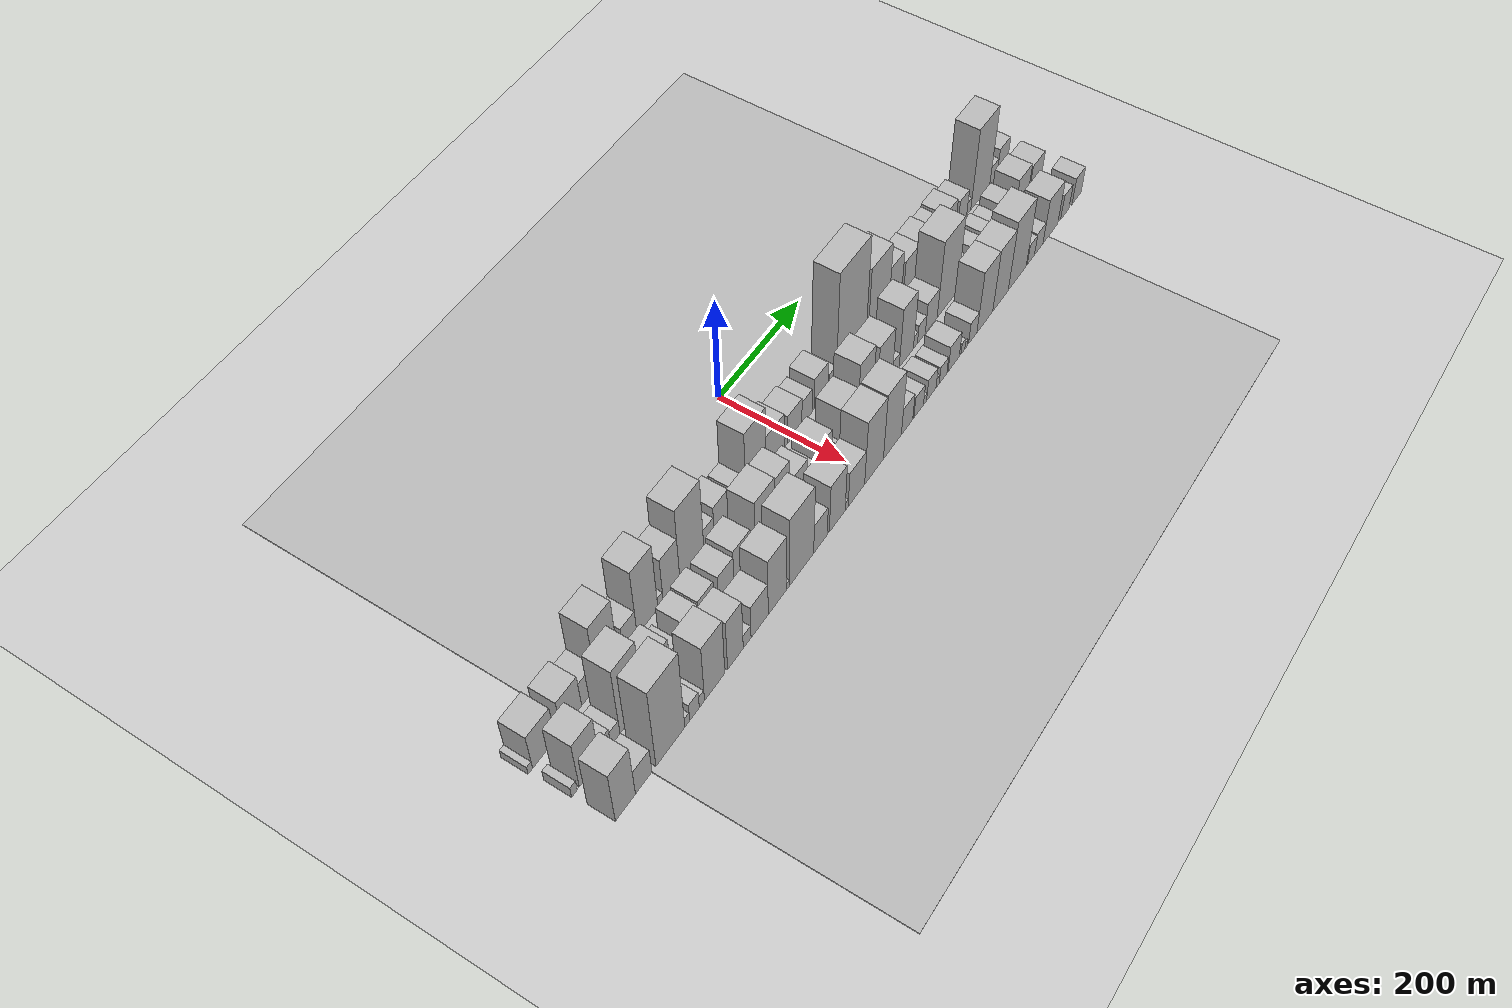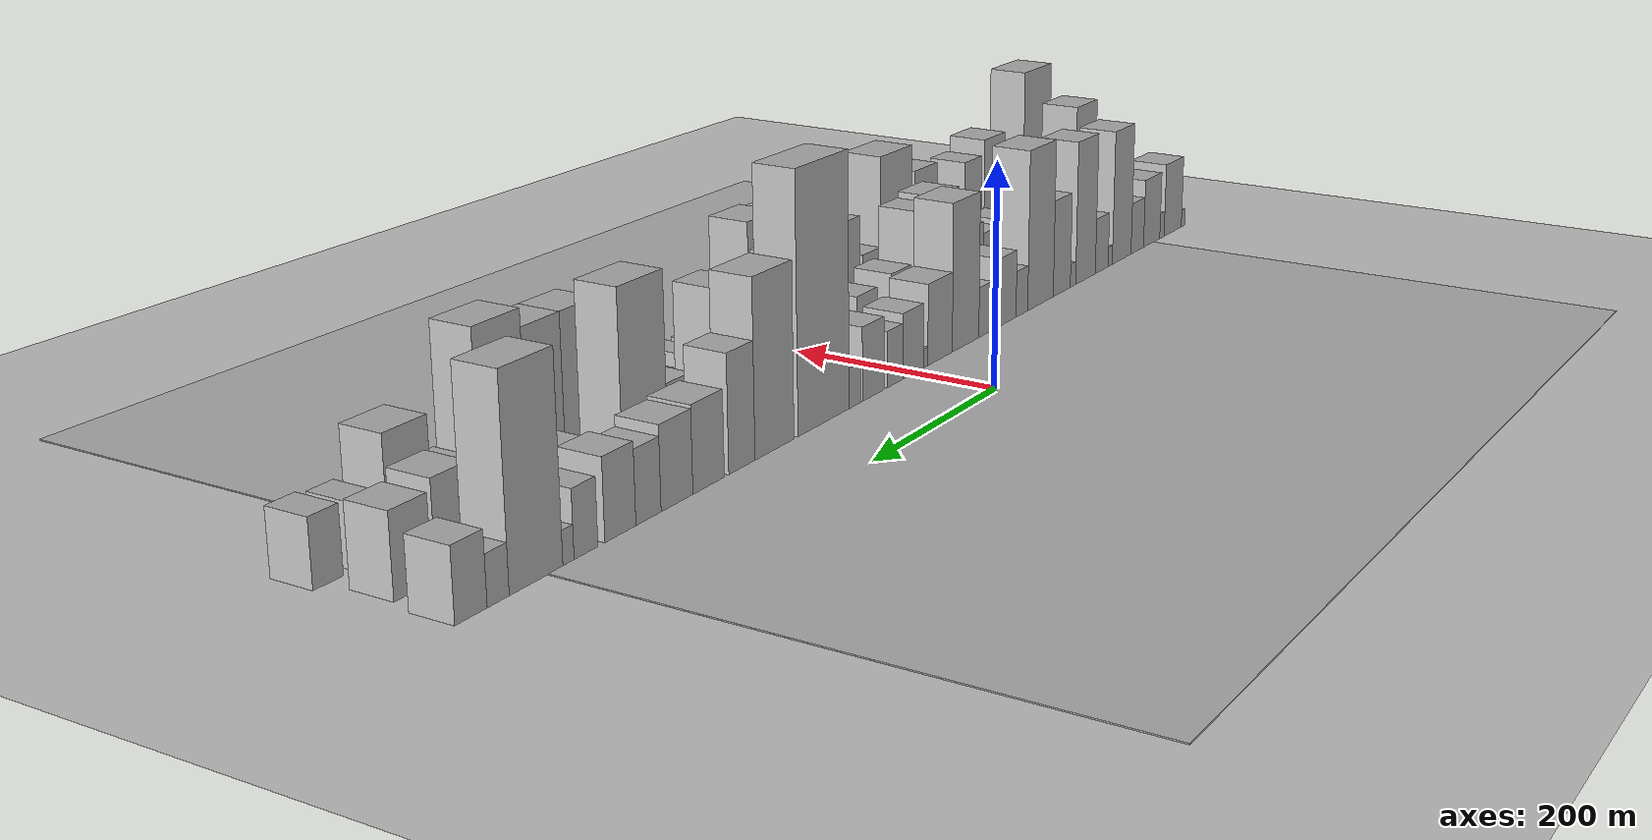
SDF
<?xml version="1.0" encoding="utf-8"?>

<sdf version="1.6">

   <world name="default">

      <gui fullscreen="0">

         <camera name="user_camera">

            <pose>-15 0 4.57585 0 0 0</pose>

            <view_controller>orbit</view_controller>

         </camera>

      </gui>

      <scene>

         <sky>

           <clouds>

             <speed>12</speed>

           </clouds>

         </sky>

         <ambient>0.4 0.4 0.4 1</ambient>

         <background>0.7 0.7 0.7 1</background>

         <shadows>1</shadows>

      </scene>

      <gravity>0 0 -9.8066</gravity>

      <magnetic_field>6e-06 2.3e-05 -4.2e-05</magnetic_field>

      <physics default="0" name="default_physics" type="ode">

         <ode>

            <solver>

               <type>quick</type>

               <iters>10</iters>

               <sor>1.0</sor>

               <use_dynamic_moi_rescaling>0</use_dynamic_moi_rescaling>

            </solver>

            <constraints>

               <cfm>0</cfm>

               <erp>0.2</erp>

               <contact_max_correcting_vel>100</contact_max_correcting_vel>

               <contact_surface_layer>0.001</contact_surface_layer>

            </constraints>

         </ode>

         <max_step_size>0.004</max_step_size>

         <real_time_factor>1</real_time_factor>

         <real_time_update_rate>250</real_time_update_rate>

      </physics>

      <light name="sun" type="directional">

         <cast_shadows>1</cast_shadows>

         <pose>0 0 10 0 0 0</pose>

         <diffuse>0.8 0.8 0.8 1</diffuse>

         <specular>0.2 0.2 0.2 1</specular>

         <attenuation>

            <range>1000</range>

            <constant>0.9</constant>

            <linear>0.01</linear>

            <quadratic>0.001</quadratic>

         </attenuation>

         <direction>-0.5 0.1 -0.9</direction>

      </light>

      <include>

         <name>ground_plane_1</name>

         <uri>model://HANNAS_ground_plane</uri>

         <pose>0 0 0  0 0 0</pose>

      </include>

      <include>

         <name>ground_plane_2</name>

         <uri>model://HANNAS_ground_plane</uri>

         <pose>100 0 0  0 0 0</pose>

      </include>

      <model name="building_1">

         <static>1</static>

         <pose frame="">100.0000 -575.5861 0 0.000000 0.000000 0.000000</pose>

         <link name="link">

            <pose frame="">0 0 9.00 0 0 0</pose>

            <collision name="collision">

               <geometry>

                  <box>

                     <size>40.0000 8.8277 18.0000</size>

                  </box>

               </geometry>

               <max_contacts>10</max_contacts>

               <surface>

                  <contact>

                     <ode/>

                  </contact>

                  <bounce/>

                  <friction>

                     <torsional>

                        <ode/>

                     </torsional>

                     <ode/>

                  </friction>

               </surface>

            </collision>

            <visual name="visual">

               <cast_shadows>0</cast_shadows>

               <geometry>

                  <box>

                     <size>40.0000 8.8277 18.0000</size>

                  </box>

               </geometry>

               <material>

                  <script>

                     <uri>model://HANNAS_wall/materials/scripts</uri>

                     <uri>model://HANNAS_wall/materials/textures</uri>

                     <name>vrc/HANNAS_wall</name>

                  </script>

               </material>

            </visual>

            <self_collide>0</self_collide>

            <enable_wind>0</enable_wind>

            <kinematic>0</kinematic>

         </link>

      </model>

      <model name="building_2">

         <static>1</static>

         <pose frame="">100.0000 -548.8549 0 0.000000 0.000000 0.000000</pose>

         <link name="link">

            <pose frame="">0 0 39.00 0 0 0</pose>

            <collision name="collision">

               <geometry>

                  <box>

                     <size>40.0000 44.6348 78.0000</size>

                  </box>

               </geometry>

               <max_contacts>10</max_contacts>

               <surface>

                  <contact>

                     <ode/>

                  </contact>

                  <bounce/>

                  <friction>

                     <torsional>

                        <ode/>

                     </torsional>

                     <ode/>

                  </friction>

               </surface>

            </collision>

            <visual name="visual">

               <cast_shadows>0</cast_shadows>

               <geometry>

                  <box>

                     <size>40.0000 44.6348 78.0000</size>

                  </box>

               </geometry>

               <material>

                  <script>

                     <uri>model://HANNAS_wall/materials/scripts</uri>

                     <uri>model://HANNAS_wall/materials/textures</uri>

                     <name>vrc/HANNAS_wall</name>

                  </script>

               </material>

            </visual>

            <self_collide>0</self_collide>

            <enable_wind>0</enable_wind>

            <kinematic>0</kinematic>

         </link>

      </model>

      <model name="building_3">

         <static>1</static>

         <pose frame="">100.0000 -520.9518 0 0.000000 0.000000 0.000000</pose>

         <link name="link">

            <pose frame="">0 0 13.50 0 0 0</pose>

            <collision name="collision">

               <geometry>

                  <box>

                     <size>40.0000 11.1714 27.0000</size>

                  </box>

               </geometry>

               <max_contacts>10</max_contacts>

               <surface>

                  <contact>

                     <ode/>

                  </contact>

                  <bounce/>

                  <friction>

                     <torsional>

                        <ode/>

                     </torsional>

                     <ode/>

                  </friction>

               </surface>

            </collision>

            <visual name="visual">

               <cast_shadows>0</cast_shadows>

               <geometry>

                  <box>

                     <size>40.0000 11.1714 27.0000</size>

                  </box>

               </geometry>

               <material>

                  <script>

                     <uri>model://HANNAS_wall/materials/scripts</uri>

                     <uri>model://HANNAS_wall/materials/textures</uri>

                     <name>vrc/HANNAS_wall</name>

                  </script>

               </material>

            </visual>

            <self_collide>0</self_collide>

            <enable_wind>0</enable_wind>

            <kinematic>0</kinematic>

         </link>

      </model>

      <model name="building_4">

         <static>1</static>

         <pose frame="">100.0000 -495.0669 0 0.000000 0.000000 0.000000</pose>

         <link name="link">

            <pose frame="">0 0 36.00 0 0 0</pose>

            <collision name="collision">

               <geometry>

                  <box>

                     <size>40.0000 40.5984 72.0000</size>

                  </box>

               </geometry>

               <max_contacts>10</max_contacts>

               <surface>

                  <contact>

                     <ode/>

                  </contact>

                  <bounce/>

                  <friction>

                     <torsional>

                        <ode/>

                     </torsional>

                     <ode/>

                  </friction>

               </surface>

            </collision>

            <visual name="visual">

               <cast_shadows>0</cast_shadows>

               <geometry>

                  <box>

                     <size>40.0000 40.5984 72.0000</size>

                  </box>

               </geometry>

               <material>

                  <script>

                     <uri>model://HANNAS_wall/materials/scripts</uri>

                     <uri>model://HANNAS_wall/materials/textures</uri>

                     <name>vrc/HANNAS_wall</name>

                  </script>

               </material>

            </visual>

            <self_collide>0</self_collide>

            <enable_wind>0</enable_wind>

            <kinematic>0</kinematic>

         </link>

      </model>

      <model name="building_5">

         <static>1</static>

         <pose frame="">100.0000 -459.3579 0 0.000000 0.000000 0.000000</pose>

         <link name="link">

            <pose frame="">0 0 27.00 0 0 0</pose>

            <collision name="collision">

               <geometry>

                  <box>

                     <size>40.0000 30.8197 54.0000</size>

                  </box>

               </geometry>

               <max_contacts>10</max_contacts>

               <surface>

                  <contact>

                     <ode/>

                  </contact>

                  <bounce/>

                  <friction>

                     <torsional>

                        <ode/>

                     </torsional>

                     <ode/>

                  </friction>

               </surface>

            </collision>

            <visual name="visual">

               <cast_shadows>0</cast_shadows>

               <geometry>

                  <box>

                     <size>40.0000 30.8197 54.0000</size>

                  </box>

               </geometry>

               <material>

                  <script>

                     <uri>model://HANNAS_wall/materials/scripts</uri>

                     <uri>model://HANNAS_wall/materials/textures</uri>

                     <name>vrc/HANNAS_wall</name>

                  </script>

               </material>

            </visual>

            <self_collide>0</self_collide>

            <enable_wind>0</enable_wind>

            <kinematic>0</kinematic>

         </link>

      </model>

      <model name="building_6">

         <static>1</static>

         <pose frame="">100.0000 -421.6280 0 0.000000 0.000000 0.000000</pose>

         <link name="link">

            <pose frame="">0 0 69.00 0 0 0</pose>

            <collision name="collision">

               <geometry>

                  <box>

                     <size>40.0000 44.6402 138.0000</size>

                  </box>

               </geometry>

               <max_contacts>10</max_contacts>

               <surface>

                  <contact>

                     <ode/>

                  </contact>

                  <bounce/>

                  <friction>

                     <torsional>

                        <ode/>

                     </torsional>

                     <ode/>

                  </friction>

               </surface>

            </collision>

            <visual name="visual">

               <cast_shadows>0</cast_shadows>

               <geometry>

                  <box>

                     <size>40.0000 44.6402 138.0000</size>

                  </box>

               </geometry>

               <material>

                  <script>

                     <uri>model://HANNAS_wall/materials/scripts</uri>

                     <uri>model://HANNAS_wall/materials/textures</uri>

                     <name>vrc/HANNAS_wall</name>

                  </script>

               </material>

            </visual>

            <self_collide>0</self_collide>

            <enable_wind>0</enable_wind>

            <kinematic>0</kinematic>

         </link>

      </model>

      <model name="building_7">

         <static>1</static>

         <pose frame="">100.0000 -394.4389 0 0.000000 0.000000 0.000000</pose>

         <link name="link">

            <pose frame="">0 0 10.50 0 0 0</pose>

            <collision name="collision">

               <geometry>

                  <box>

                     <size>40.0000 9.7380 21.0000</size>

                  </box>

               </geometry>

               <max_contacts>10</max_contacts>

               <surface>

                  <contact>

                     <ode/>

                  </contact>

                  <bounce/>

                  <friction>

                     <torsional>

                        <ode/>

                     </torsional>

                     <ode/>

                  </friction>

               </surface>

            </collision>

            <visual name="visual">

               <cast_shadows>0</cast_shadows>

               <geometry>

                  <box>

                     <size>40.0000 9.7380 21.0000</size>

                  </box>

               </geometry>

               <material>

                  <script>

                     <uri>model://HANNAS_wall/materials/scripts</uri>

                     <uri>model://HANNAS_wall/materials/textures</uri>

                     <name>vrc/HANNAS_wall</name>

                  </script>

               </material>

            </visual>

            <self_collide>0</self_collide>

            <enable_wind>0</enable_wind>

            <kinematic>0</kinematic>

         </link>

      </model>

      <model name="building_8">

         <static>1</static>

         <pose frame="">100.0000 -374.8891 0 0.000000 0.000000 0.000000</pose>

         <link name="link">

            <pose frame="">0 0 28.50 0 0 0</pose>

            <collision name="collision">

               <geometry>

                  <box>

                     <size>40.0000 29.3615 57.0000</size>

                  </box>

               </geometry>

               <max_contacts>10</max_contacts>

               <surface>

                  <contact>

                     <ode/>

                  </contact>

                  <bounce/>

                  <friction>

                     <torsional>

                        <ode/>

                     </torsional>

                     <ode/>

                  </friction>

               </surface>

            </collision>

            <visual name="visual">

               <cast_shadows>0</cast_shadows>

               <geometry>

                  <box>

                     <size>40.0000 29.3615 57.0000</size>

                  </box>

               </geometry>

               <material>

                  <script>

                     <uri>model://HANNAS_wall/materials/scripts</uri>

                     <uri>model://HANNAS_wall/materials/textures</uri>

                     <name>vrc/HANNAS_wall</name>

                  </script>

               </material>

            </visual>

            <self_collide>0</self_collide>

            <enable_wind>0</enable_wind>

            <kinematic>0</kinematic>

         </link>

      </model>

      <model name="building_9">

         <static>1</static>

         <pose frame="">100.0000 -338.0210 0 0.000000 0.000000 0.000000</pose>

         <link name="link">

            <pose frame="">0 0 72.00 0 0 0</pose>

            <collision name="collision">

               <geometry>

                  <box>

                     <size>40.0000 44.3749 144.0000</size>

                  </box>

               </geometry>

               <max_contacts>10</max_contacts>

               <surface>

                  <contact>

                     <ode/>

                  </contact>

                  <bounce/>

                  <friction>

                     <torsional>

                        <ode/>

                     </torsional>

                     <ode/>

                  </friction>

               </surface>

            </collision>

            <visual name="visual">

               <cast_shadows>0</cast_shadows>

               <geometry>

                  <box>

                     <size>40.0000 44.3749 144.0000</size>

                  </box>

               </geometry>

               <material>

                  <script>

                     <uri>model://HANNAS_wall/materials/scripts</uri>

                     <uri>model://HANNAS_wall/materials/textures</uri>

                     <name>vrc/HANNAS_wall</name>

                  </script>

               </material>

            </visual>

            <self_collide>0</self_collide>

            <enable_wind>0</enable_wind>

            <kinematic>0</kinematic>

         </link>

      </model>

      <model name="building_10">

         <static>1</static>

         <pose frame="">100.0000 -310.0558 0 0.000000 0.000000 0.000000</pose>

         <link name="link">

            <pose frame="">0 0 12.00 0 0 0</pose>

            <collision name="collision">

               <geometry>

                  <box>

                     <size>40.0000 11.5555 24.0000</size>

                  </box>

               </geometry>

               <max_contacts>10</max_contacts>

               <surface>

                  <contact>

                     <ode/>

                  </contact>

                  <bounce/>

                  <friction>

                     <torsional>

                        <ode/>

                     </torsional>

                     <ode/>

                  </friction>

               </surface>

            </collision>

            <visual name="visual">

               <cast_shadows>0</cast_shadows>

               <geometry>

                  <box>

                     <size>40.0000 11.5555 24.0000</size>

                  </box>

               </geometry>

               <material>

                  <script>

                     <uri>model://HANNAS_wall/materials/scripts</uri>

                     <uri>model://HANNAS_wall/materials/textures</uri>

                     <name>vrc/HANNAS_wall</name>

                  </script>

               </material>

            </visual>

            <self_collide>0</self_collide>

            <enable_wind>0</enable_wind>

            <kinematic>0</kinematic>

         </link>

      </model>

      <model name="building_11">

         <static>1</static>

         <pose frame="">100.0000 -285.9125 0 0.000000 0.000000 0.000000</pose>

         <link name="link">

            <pose frame="">0 0 48.00 0 0 0</pose>

            <collision name="collision">

               <geometry>

                  <box>

                     <size>40.0000 36.7311 96.0000</size>

                  </box>

               </geometry>

               <max_contacts>10</max_contacts>

               <surface>

                  <contact>

                     <ode/>

                  </contact>

                  <bounce/>

                  <friction>

                     <torsional>

                        <ode/>

                     </torsional>

                     <ode/>

                  </friction>

               </surface>

            </collision>

            <visual name="visual">

               <cast_shadows>0</cast_shadows>

               <geometry>

                  <box>

                     <size>40.0000 36.7311 96.0000</size>

                  </box>

               </geometry>

               <material>

                  <script>

                     <uri>model://HANNAS_wall/materials/scripts</uri>

                     <uri>model://HANNAS_wall/materials/textures</uri>

                     <name>vrc/HANNAS_wall</name>

                  </script>

               </material>

            </visual>

            <self_collide>0</self_collide>

            <enable_wind>0</enable_wind>

            <kinematic>0</kinematic>

         </link>

      </model>

      <model name="building_12">

         <static>1</static>

         <pose frame="">100.0000 -240.7987 0 0.000000 0.000000 0.000000</pose>

         <link name="link">

            <pose frame="">0 0 78.00 0 0 0</pose>

            <collision name="collision">

               <geometry>

                  <box>

                     <size>40.0000 53.4963 156.0000</size>

                  </box>

               </geometry>

               <max_contacts>10</max_contacts>

               <surface>

                  <contact>

                     <ode/>

                  </contact>

                  <bounce/>

                  <friction>

                     <torsional>

                        <ode/>

                     </torsional>

                     <ode/>

                  </friction>

               </surface>

            </collision>

            <visual name="visual">

               <cast_shadows>0</cast_shadows>

               <geometry>

                  <box>

                     <size>40.0000 53.4963 156.0000</size>

                  </box>

               </geometry>

               <material>

                  <script>

                     <uri>model://HANNAS_wall/materials/scripts</uri>

                     <uri>model://HANNAS_wall/materials/textures</uri>

                     <name>vrc/HANNAS_wall</name>

                  </script>

               </material>

            </visual>

            <self_collide>0</self_collide>

            <enable_wind>0</enable_wind>

            <kinematic>0</kinematic>

         </link>

      </model>

      <model name="building_13">

         <static>1</static>

         <pose frame="">100.0000 -202.2529 0 0.000000 0.000000 0.000000</pose>

         <link name="link">

            <pose frame="">0 0 22.50 0 0 0</pose>

            <collision name="collision">

               <geometry>

                  <box>

                     <size>40.0000 23.5954 45.0000</size>

                  </box>

               </geometry>

               <max_contacts>10</max_contacts>

               <surface>

                  <contact>

                     <ode/>

                  </contact>

                  <bounce/>

                  <friction>

                     <torsional>

                        <ode/>

                     </torsional>

                     <ode/>

                  </friction>

               </surface>

            </collision>

            <visual name="visual">

               <cast_shadows>0</cast_shadows>

               <geometry>

                  <box>

                     <size>40.0000 23.5954 45.0000</size>

                  </box>

               </geometry>

               <material>

                  <script>

                     <uri>model://HANNAS_wall/materials/scripts</uri>

                     <uri>model://HANNAS_wall/materials/textures</uri>

                     <name>vrc/HANNAS_wall</name>

                  </script>

               </material>

            </visual>

            <self_collide>0</self_collide>

            <enable_wind>0</enable_wind>

            <kinematic>0</kinematic>

         </link>

      </model>

      <model name="building_14">

         <static>1</static>

         <pose frame="">100.0000 -173.3818 0 0.000000 0.000000 0.000000</pose>

         <link name="link">

            <pose frame="">0 0 33.00 0 0 0</pose>

            <collision name="collision">

               <geometry>

                  <box>

                     <size>40.0000 34.1467 66.0000</size>

                  </box>

               </geometry>

               <max_contacts>10</max_contacts>

               <surface>

                  <contact>

                     <ode/>

                  </contact>

                  <bounce/>

                  <friction>

                     <torsional>

                        <ode/>

                     </torsional>

                     <ode/>

                  </friction>

               </surface>

            </collision>

            <visual name="visual">

               <cast_shadows>0</cast_shadows>

               <geometry>

                  <box>

                     <size>40.0000 34.1467 66.0000</size>

                  </box>

               </geometry>

               <material>

                  <script>

                     <uri>model://HANNAS_wall/materials/scripts</uri>

                     <uri>model://HANNAS_wall/materials/textures</uri>

                     <name>vrc/HANNAS_wall</name>

                  </script>

               </material>

            </visual>

            <self_collide>0</self_collide>

            <enable_wind>0</enable_wind>

            <kinematic>0</kinematic>

         </link>

      </model>

      <model name="building_15">

         <static>1</static>

         <pose frame="">100.0000 -148.1046 0 0.000000 0.000000 0.000000</pose>

         <link name="link">

            <pose frame="">0 0 12.00 0 0 0</pose>

            <collision name="collision">

               <geometry>

                  <box>

                     <size>40.0000 10.4078 24.0000</size>

                  </box>

               </geometry>

               <max_contacts>10</max_contacts>

               <surface>

                  <contact>

                     <ode/>

                  </contact>

                  <bounce/>

                  <friction>

                     <torsional>

                        <ode/>

                     </torsional>

                     <ode/>

                  </friction>

               </surface>

            </collision>

            <visual name="visual">

               <cast_shadows>0</cast_shadows>

               <geometry>

                  <box>

                     <size>40.0000 10.4078 24.0000</size>

                  </box>

               </geometry>

               <material>

                  <script>

                     <uri>model://HANNAS_wall/materials/scripts</uri>

                     <uri>model://HANNAS_wall/materials/textures</uri>

                     <name>vrc/HANNAS_wall</name>

                  </script>

               </material>

            </visual>

            <self_collide>0</self_collide>

            <enable_wind>0</enable_wind>

            <kinematic>0</kinematic>

         </link>

      </model>

      <model name="building_16">

         <static>1</static>

         <pose frame="">100.0000 -130.3756 0 0.000000 0.000000 0.000000</pose>

         <link name="link">

            <pose frame="">0 0 24.00 0 0 0</pose>

            <collision name="collision">

               <geometry>

                  <box>

                     <size>40.0000 25.0502 48.0000</size>

                  </box>

               </geometry>

               <max_contacts>10</max_contacts>

               <surface>

                  <contact>

                     <ode/>

                  </contact>

                  <bounce/>

                  <friction>

                     <torsional>

                        <ode/>

                     </torsional>

                     <ode/>

                  </friction>

               </surface>

            </collision>

            <visual name="visual">

               <cast_shadows>0</cast_shadows>

               <geometry>

                  <box>

                     <size>40.0000 25.0502 48.0000</size>

                  </box>

               </geometry>

               <material>

                  <script>

                     <uri>model://HANNAS_wall/materials/scripts</uri>

                     <uri>model://HANNAS_wall/materials/textures</uri>

                     <name>vrc/HANNAS_wall</name>

                  </script>

               </material>

            </visual>

            <self_collide>0</self_collide>

            <enable_wind>0</enable_wind>

            <kinematic>0</kinematic>

         </link>

      </model>

      <model name="building_17">

         <static>1</static>

         <pose frame="">100.0000 -93.1623 0 0.000000 0.000000 0.000000</pose>

         <link name="link">

            <pose frame="">0 0 69.00 0 0 0</pose>

            <collision name="collision">

               <geometry>

                  <box>

                     <size>40.0000 49.3765 138.0000</size>

                  </box>

               </geometry>

               <max_contacts>10</max_contacts>

               <surface>

                  <contact>

                     <ode/>

                  </contact>

                  <bounce/>

                  <friction>

                     <torsional>

                        <ode/>

                     </torsional>

                     <ode/>

                  </friction>

               </surface>

            </collision>

            <visual name="visual">

               <cast_shadows>0</cast_shadows>

               <geometry>

                  <box>

                     <size>40.0000 49.3765 138.0000</size>

                  </box>

               </geometry>

               <material>

                  <script>

                     <uri>model://HANNAS_wall/materials/scripts</uri>

                     <uri>model://HANNAS_wall/materials/textures</uri>

                     <name>vrc/HANNAS_wall</name>

                  </script>

               </material>

            </visual>

            <self_collide>0</self_collide>

            <enable_wind>0</enable_wind>

            <kinematic>0</kinematic>

         </link>

      </model>

      <model name="building_18">

         <static>1</static>

         <pose frame="">100.0000 -46.5483 0 0.000000 0.000000 0.000000</pose>

         <link name="link">

            <pose frame="">0 0 37.50 0 0 0</pose>

            <collision name="collision">

               <geometry>

                  <box>

                     <size>40.0000 43.8515 75.0000</size>

                  </box>

               </geometry>

               <max_contacts>10</max_contacts>

               <surface>

                  <contact>

                     <ode/>

                  </contact>

                  <bounce/>

                  <friction>

                     <torsional>

                        <ode/>

                     </torsional>

                     <ode/>

                  </friction>

               </surface>

            </collision>

            <visual name="visual">

               <cast_shadows>0</cast_shadows>

               <geometry>

                  <box>

                     <size>40.0000 43.8515 75.0000</size>

                  </box>

               </geometry>

               <material>

                  <script>

                     <uri>model://HANNAS_wall/materials/scripts</uri>

                     <uri>model://HANNAS_wall/materials/textures</uri>

                     <name>vrc/HANNAS_wall</name>

                  </script>

               </material>

            </visual>

            <self_collide>0</self_collide>

            <enable_wind>0</enable_wind>

            <kinematic>0</kinematic>

         </link>

      </model>

      <model name="building_19">

         <static>1</static>

         <pose frame="">100.0000 -20.6367 0 0.000000 0.000000 0.000000</pose>

         <link name="link">

            <pose frame="">0 0 9.00 0 0 0</pose>

            <collision name="collision">

               <geometry>

                  <box>

                     <size>40.0000 7.9717 18.0000</size>

                  </box>

               </geometry>

               <max_contacts>10</max_contacts>

               <surface>

                  <contact>

                     <ode/>

                  </contact>

                  <bounce/>

                  <friction>

                     <torsional>

                        <ode/>

                     </torsional>

                     <ode/>

                  </friction>

               </surface>

            </collision>

            <visual name="visual">

               <cast_shadows>0</cast_shadows>

               <geometry>

                  <box>

                     <size>40.0000 7.9717 18.0000</size>

                  </box>

               </geometry>

               <material>

                  <script>

                     <uri>model://HANNAS_wall/materials/scripts</uri>

                     <uri>model://HANNAS_wall/materials/textures</uri>

                     <name>vrc/HANNAS_wall</name>

                  </script>

               </material>

            </visual>

            <self_collide>0</self_collide>

            <enable_wind>0</enable_wind>

            <kinematic>0</kinematic>

         </link>

      </model>

      <model name="building_20">

         <static>1</static>

         <pose frame="">100.0000 1.1828 0 0.000000 0.000000 0.000000</pose>

         <link name="link">

            <pose frame="">0 0 30.00 0 0 0</pose>

            <collision name="collision">

               <geometry>

                  <box>

                     <size>40.0000 35.6672 60.0000</size>

                  </box>

               </geometry>

               <max_contacts>10</max_contacts>

               <surface>

                  <contact>

                     <ode/>

                  </contact>

                  <bounce/>

                  <friction>

                     <torsional>

                        <ode/>

                     </torsional>

                     <ode/>

                  </friction>

               </surface>

            </collision>

            <visual name="visual">

               <cast_shadows>0</cast_shadows>

               <geometry>

                  <box>

                     <size>40.0000 35.6672 60.0000</size>

                  </box>

               </geometry>

               <material>

                  <script>

                     <uri>model://HANNAS_wall/materials/scripts</uri>

                     <uri>model://HANNAS_wall/materials/textures</uri>

                     <name>vrc/HANNAS_wall</name>

                  </script>

               </material>

            </visual>

            <self_collide>0</self_collide>

            <enable_wind>0</enable_wind>

            <kinematic>0</kinematic>

         </link>

      </model>

      <model name="building_21">

         <static>1</static>

         <pose frame="">100.0000 32.1808 0 0.000000 0.000000 0.000000</pose>

         <link name="link">

            <pose frame="">0 0 25.50 0 0 0</pose>

            <collision name="collision">

               <geometry>

                  <box>

                     <size>40.0000 26.3290 51.0000</size>

                  </box>

               </geometry>

               <max_contacts>10</max_contacts>

               <surface>

                  <contact>

                     <ode/>

                  </contact>

                  <bounce/>

                  <friction>

                     <torsional>

                        <ode/>

                     </torsional>

                     <ode/>

                  </friction>

               </surface>

            </collision>

            <visual name="visual">

               <cast_shadows>0</cast_shadows>

               <geometry>

                  <box>

                     <size>40.0000 26.3290 51.0000</size>

                  </box>

               </geometry>

               <material>

                  <script>

                     <uri>model://HANNAS_wall/materials/scripts</uri>

                     <uri>model://HANNAS_wall/materials/textures</uri>

                     <name>vrc/HANNAS_wall</name>

                  </script>

               </material>

            </visual>

            <self_collide>0</self_collide>

            <enable_wind>0</enable_wind>

            <kinematic>0</kinematic>

         </link>

      </model>

      <model name="building_22">

         <static>1</static>

         <pose frame="">100.0000 67.8488 0 0.000000 0.000000 0.000000</pose>

         <link name="link">

            <pose frame="">0 0 33.00 0 0 0</pose>

            <collision name="collision">

               <geometry>

                  <box>

                     <size>40.0000 35.0070 66.0000</size>

                  </box>

               </geometry>

               <max_contacts>10</max_contacts>

               <surface>

                  <contact>

                     <ode/>

                  </contact>

                  <bounce/>

                  <friction>

                     <torsional>

                        <ode/>

                     </torsional>

                     <ode/>

                  </friction>

               </surface>

            </collision>

            <visual name="visual">

               <cast_shadows>0</cast_shadows>

               <geometry>

                  <box>

                     <size>40.0000 35.0070 66.0000</size>

                  </box>

               </geometry>

               <material>

                  <script>

                     <uri>model://HANNAS_wall/materials/scripts</uri>

                     <uri>model://HANNAS_wall/materials/textures</uri>

                     <name>vrc/HANNAS_wall</name>

                  </script>

               </material>

            </visual>

            <self_collide>0</self_collide>

            <enable_wind>0</enable_wind>

            <kinematic>0</kinematic>

         </link>

      </model>

      <model name="building_23">

         <static>1</static>

         <pose frame="">100.0000 97.4326 0 0.000000 0.000000 0.000000</pose>

         <link name="link">

            <pose frame="">0 0 18.00 0 0 0</pose>

            <collision name="collision">

               <geometry>

                  <box>

                     <size>40.0000 18.1607 36.0000</size>

                  </box>

               </geometry>

               <max_contacts>10</max_contacts>

               <surface>

                  <contact>

                     <ode/>

                  </contact>

                  <bounce/>

                  <friction>

                     <torsional>

                        <ode/>

                     </torsional>

                     <ode/>

                  </friction>

               </surface>

            </collision>

            <visual name="visual">

               <cast_shadows>0</cast_shadows>

               <geometry>

                  <box>

                     <size>40.0000 18.1607 36.0000</size>

                  </box>

               </geometry>

               <material>

                  <script>

                     <uri>model://HANNAS_wall/materials/scripts</uri>

                     <uri>model://HANNAS_wall/materials/textures</uri>

                     <name>vrc/HANNAS_wall</name>

                  </script>

               </material>

            </visual>

            <self_collide>0</self_collide>

            <enable_wind>0</enable_wind>

            <kinematic>0</kinematic>

         </link>

      </model>

      <model name="building_24">

         <static>1</static>

         <pose frame="">100.0000 145.5069 0 0.000000 0.000000 0.000000</pose>

         <link name="link">

            <pose frame="">0 0 111.00 0 0 0</pose>

            <collision name="collision">

               <geometry>

                  <box>

                     <size>40.0000 77.9878 222.0000</size>

                  </box>

               </geometry>

               <max_contacts>10</max_contacts>

               <surface>

                  <contact>

                     <ode/>

                  </contact>

                  <bounce/>

                  <friction>

                     <torsional>

                        <ode/>

                     </torsional>

                     <ode/>

                  </friction>

               </surface>

            </collision>

            <visual name="visual">

               <cast_shadows>0</cast_shadows>

               <geometry>

                  <box>

                     <size>40.0000 77.9878 222.0000</size>

                  </box>

               </geometry>

               <material>

                  <script>

                     <uri>model://HANNAS_wall/materials/scripts</uri>

                     <uri>model://HANNAS_wall/materials/textures</uri>

                     <name>vrc/HANNAS_wall</name>

                  </script>

               </material>

            </visual>

            <self_collide>0</self_collide>

            <enable_wind>0</enable_wind>

            <kinematic>0</kinematic>

         </link>

      </model>

      <model name="building_25">

         <static>1</static>

         <pose frame="">100.0000 218.3089 0 0.000000 0.000000 0.000000</pose>

         <link name="link">

            <pose frame="">0 0 75.00 0 0 0</pose>

            <collision name="collision">

               <geometry>

                  <box>

                     <size>40.0000 55.6163 150.0000</size>

                  </box>

               </geometry>

               <max_contacts>10</max_contacts>

               <surface>

                  <contact>

                     <ode/>

                  </contact>

                  <bounce/>

                  <friction>

                     <torsional>

                        <ode/>

                     </torsional>

                     <ode/>

                  </friction>

               </surface>

            </collision>

            <visual name="visual">

               <cast_shadows>0</cast_shadows>

               <geometry>

                  <box>

                     <size>40.0000 55.6163 150.0000</size>

                  </box>

               </geometry>

               <material>

                  <script>

                     <uri>model://HANNAS_wall/materials/scripts</uri>

                     <uri>model://HANNAS_wall/materials/textures</uri>

                     <name>vrc/HANNAS_wall</name>

                  </script>

               </material>

            </visual>

            <self_collide>0</self_collide>

            <enable_wind>0</enable_wind>

            <kinematic>0</kinematic>

         </link>

      </model>

      <model name="building_26">

         <static>1</static>

         <pose frame="">100.0000 264.1059 0 0.000000 0.000000 0.000000</pose>

         <link name="link">

            <pose frame="">0 0 49.50 0 0 0</pose>

            <collision name="collision">

               <geometry>

                  <box>

                     <size>40.0000 35.9778 99.0000</size>

                  </box>

               </geometry>

               <max_contacts>10</max_contacts>

               <surface>

                  <contact>

                     <ode/>

                  </contact>

                  <bounce/>

                  <friction>

                     <torsional>

                        <ode/>

                     </torsional>

                     <ode/>

                  </friction>

               </surface>

            </collision>

            <visual name="visual">

               <cast_shadows>0</cast_shadows>

               <geometry>

                  <box>

                     <size>40.0000 35.9778 99.0000</size>

                  </box>

               </geometry>

               <material>

                  <script>

                     <uri>model://HANNAS_wall/materials/scripts</uri>

                     <uri>model://HANNAS_wall/materials/textures</uri>

                     <name>vrc/HANNAS_wall</name>

                  </script>

               </material>

            </visual>

            <self_collide>0</self_collide>

            <enable_wind>0</enable_wind>

            <kinematic>0</kinematic>

         </link>

      </model>

      <model name="building_27">

         <static>1</static>

         <pose frame="">100.0000 308.7166 0 0.000000 0.000000 0.000000</pose>

         <link name="link">

            <pose frame="">0 0 36.00 0 0 0</pose>

            <collision name="collision">

               <geometry>

                  <box>

                     <size>40.0000 41.2436 72.0000</size>

                  </box>

               </geometry>

               <max_contacts>10</max_contacts>

               <surface>

                  <contact>

                     <ode/>

                  </contact>

                  <bounce/>

                  <friction>

                     <torsional>

                        <ode/>

                     </torsional>

                     <ode/>

                  </friction>

               </surface>

            </collision>

            <visual name="visual">

               <cast_shadows>0</cast_shadows>

               <geometry>

                  <box>

                     <size>40.0000 41.2436 72.0000</size>

                  </box>

               </geometry>

               <material>

                  <script>

                     <uri>model://HANNAS_wall/materials/scripts</uri>

                     <uri>model://HANNAS_wall/materials/textures</uri>

                     <name>vrc/HANNAS_wall</name>

                  </script>

               </material>

            </visual>

            <self_collide>0</self_collide>

            <enable_wind>0</enable_wind>

            <kinematic>0</kinematic>

         </link>

      </model>

      <model name="building_28">

         <static>1</static>

         <pose frame="">100.0000 349.4230 0 0.000000 0.000000 0.000000</pose>

         <link name="link">

            <pose frame="">0 0 34.50 0 0 0</pose>

            <collision name="collision">

               <geometry>

                  <box>

                     <size>40.0000 40.1692 69.0000</size>

                  </box>

               </geometry>

               <max_contacts>10</max_contacts>

               <surface>

                  <contact>

                     <ode/>

                  </contact>

                  <bounce/>

                  <friction>

                     <torsional>

                        <ode/>

                     </torsional>

                     <ode/>

                  </friction>

               </surface>

            </collision>

            <visual name="visual">

               <cast_shadows>0</cast_shadows>

               <geometry>

                  <box>

                     <size>40.0000 40.1692 69.0000</size>

                  </box>

               </geometry>

               <material>

                  <script>

                     <uri>model://HANNAS_wall/materials/scripts</uri>

                     <uri>model://HANNAS_wall/materials/textures</uri>

                     <name>vrc/HANNAS_wall</name>

                  </script>

               </material>

            </visual>

            <self_collide>0</self_collide>

            <enable_wind>0</enable_wind>

            <kinematic>0</kinematic>

         </link>

      </model>

      <model name="building_29">

         <static>1</static>

         <pose frame="">100.0000 384.8734 0 0.000000 0.000000 0.000000</pose>

         <link name="link">

            <pose frame="">0 0 30.00 0 0 0</pose>

            <collision name="collision">

               <geometry>

                  <box>

                     <size>40.0000 30.7317 60.0000</size>

                  </box>

               </geometry>

               <max_contacts>10</max_contacts>

               <surface>

                  <contact>

                     <ode/>

                  </contact>

                  <bounce/>

                  <friction>

                     <torsional>

                        <ode/>

                     </torsional>

                     <ode/>

                  </friction>

               </surface>

            </collision>

            <visual name="visual">

               <cast_shadows>0</cast_shadows>

               <geometry>

                  <box>

                     <size>40.0000 30.7317 60.0000</size>

                  </box>

               </geometry>

               <material>

                  <script>

                     <uri>model://HANNAS_wall/materials/scripts</uri>

                     <uri>model://HANNAS_wall/materials/textures</uri>

                     <name>vrc/HANNAS_wall</name>

                  </script>

               </material>

            </visual>

            <self_collide>0</self_collide>

            <enable_wind>0</enable_wind>

            <kinematic>0</kinematic>

         </link>

      </model>

      <model name="building_30">

         <static>1</static>

         <pose frame="">100.0000 418.5343 0 0.000000 0.000000 0.000000</pose>

         <link name="link">

            <pose frame="">0 0 33.00 0 0 0</pose>

            <collision name="collision">

               <geometry>

                  <box>

                     <size>40.0000 36.5901 66.0000</size>

                  </box>

               </geometry>

               <max_contacts>10</max_contacts>

               <surface>

                  <contact>

                     <ode/>

                  </contact>

                  <bounce/>

                  <friction>

                     <torsional>

                        <ode/>

                     </torsional>

                     <ode/>

                  </friction>

               </surface>

            </collision>

            <visual name="visual">

               <cast_shadows>0</cast_shadows>

               <geometry>

                  <box>

                     <size>40.0000 36.5901 66.0000</size>

                  </box>

               </geometry>

               <material>

                  <script>

                     <uri>model://HANNAS_wall/materials/scripts</uri>

                     <uri>model://HANNAS_wall/materials/textures</uri>

                     <name>vrc/HANNAS_wall</name>

                  </script>

               </material>

            </visual>

            <self_collide>0</self_collide>

            <enable_wind>0</enable_wind>

            <kinematic>0</kinematic>

         </link>

      </model>

      <model name="building_31">

         <static>1</static>

         <pose frame="">100.0000 458.3467 0 0.000000 0.000000 0.000000</pose>

         <link name="link">

            <pose frame="">0 0 27.00 0 0 0</pose>

            <collision name="collision">

               <geometry>

                  <box>

                     <size>40.0000 27.0347 54.0000</size>

                  </box>

               </geometry>

               <max_contacts>10</max_contacts>

               <surface>

                  <contact>

                     <ode/>

                  </contact>

                  <bounce/>

                  <friction>

                     <torsional>

                        <ode/>

                     </torsional>

                     <ode/>

                  </friction>

               </surface>

            </collision>

            <visual name="visual">

               <cast_shadows>0</cast_shadows>

               <geometry>

                  <box>

                     <size>40.0000 27.0347 54.0000</size>

                  </box>

               </geometry>

               <material>

                  <script>

                     <uri>model://HANNAS_wall/materials/scripts</uri>

                     <uri>model://HANNAS_wall/materials/textures</uri>

                     <name>vrc/HANNAS_wall</name>

                  </script>

               </material>

            </visual>

            <self_collide>0</self_collide>

            <enable_wind>0</enable_wind>

            <kinematic>0</kinematic>

         </link>

      </model>

      <model name="building_32">

         <static>1</static>

         <pose frame="">100.0000 478.0838 0 0.000000 0.000000 0.000000</pose>

         <link name="link">

            <pose frame="">0 0 13.50 0 0 0</pose>

            <collision name="collision">

               <geometry>

                  <box>

                     <size>40.0000 12.4395 27.0000</size>

                  </box>

               </geometry>

               <max_contacts>10</max_contacts>

               <surface>

                  <contact>

                     <ode/>

                  </contact>

                  <bounce/>

                  <friction>

                     <torsional>

                        <ode/>

                     </torsional>

                     <ode/>

                  </friction>

               </surface>

            </collision>

            <visual name="visual">

               <cast_shadows>0</cast_shadows>

               <geometry>

                  <box>

                     <size>40.0000 12.4395 27.0000</size>

                  </box>

               </geometry>

               <material>

                  <script>

                     <uri>model://HANNAS_wall/materials/scripts</uri>

                     <uri>model://HANNAS_wall/materials/textures</uri>

                     <name>vrc/HANNAS_wall</name>

                  </script>

               </material>

            </visual>

            <self_collide>0</self_collide>

            <enable_wind>0</enable_wind>

            <kinematic>0</kinematic>

         </link>

      </model>

      <model name="building_33">

         <static>1</static>

         <pose frame="">100.0000 513.0202 0 0.000000 0.000000 0.000000</pose>

         <link name="link">

            <pose frame="">0 0 81.00 0 0 0</pose>

            <collision name="collision">

               <geometry>

                  <box>

                     <size>40.0000 57.4334 162.0000</size>

                  </box>

               </geometry>

               <max_contacts>10</max_contacts>

               <surface>

                  <contact>

                     <ode/>

                  </contact>

                  <bounce/>

                  <friction>

                     <torsional>

                        <ode/>

                     </torsional>

                     <ode/>

                  </friction>

               </surface>

            </collision>

            <visual name="visual">

               <cast_shadows>0</cast_shadows>

               <geometry>

                  <box>

                     <size>40.0000 57.4334 162.0000</size>

                  </box>

               </geometry>

               <material>

                  <script>

                     <uri>model://HANNAS_wall/materials/scripts</uri>

                     <uri>model://HANNAS_wall/materials/textures</uri>

                     <name>vrc/HANNAS_wall</name>

                  </script>

               </material>

            </visual>

            <self_collide>0</self_collide>

            <enable_wind>0</enable_wind>

            <kinematic>0</kinematic>

         </link>

      </model>

      <model name="building_34">

         <static>1</static>

         <pose frame="">100.0000 553.0574 0 0.000000 0.000000 0.000000</pose>

         <link name="link">

            <pose frame="">0 0 19.50 0 0 0</pose>

            <collision name="collision">

               <geometry>

                  <box>

                     <size>40.0000 22.6411 39.0000</size>

                  </box>

               </geometry>

               <max_contacts>10</max_contacts>

               <surface>

                  <contact>

                     <ode/>

                  </contact>

                  <bounce/>

                  <friction>

                     <torsional>

                        <ode/>

                     </torsional>

                     <ode/>

                  </friction>

               </surface>

            </collision>

            <visual name="visual">

               <cast_shadows>0</cast_shadows>

               <geometry>

                  <box>

                     <size>40.0000 22.6411 39.0000</size>

                  </box>

               </geometry>

               <material>

                  <script>

                     <uri>model://HANNAS_wall/materials/scripts</uri>

                     <uri>model://HANNAS_wall/materials/textures</uri>

                     <name>vrc/HANNAS_wall</name>

                  </script>

               </material>

            </visual>

            <self_collide>0</self_collide>

            <enable_wind>0</enable_wind>

            <kinematic>0</kinematic>

         </link>

      </model>

      <model name="building_35">

         <static>1</static>

         <pose frame="">100.0000 580.5627 0 0.000000 0.000000 0.000000</pose>

         <link name="link">

            <pose frame="">0 0 28.50 0 0 0</pose>

            <collision name="collision">

               <geometry>

                  <box>

                     <size>40.0000 32.3694 57.0000</size>

                  </box>

               </geometry>

               <max_contacts>10</max_contacts>

               <surface>

                  <contact>

                     <ode/>

                  </contact>

                  <bounce/>

                  <friction>

                     <torsional>

                        <ode/>

                     </torsional>

                     <ode/>

                  </friction>

               </surface>

            </collision>

            <visual name="visual">

               <cast_shadows>0</cast_shadows>

               <geometry>

                  <box>

                     <size>40.0000 32.3694 57.0000</size>

                  </box>

               </geometry>

               <material>

                  <script>

                     <uri>model://HANNAS_wall/materials/scripts</uri>

                     <uri>model://HANNAS_wall/materials/textures</uri>

                     <name>vrc/HANNAS_wall</name>

                  </script>

               </material>

            </visual>

            <self_collide>0</self_collide>

            <enable_wind>0</enable_wind>

            <kinematic>0</kinematic>

         </link>

      </model>

      <model name="building_36">

         <static>1</static>

         <pose frame="">160.0000 -570.5280 0 0.000000 0.000000 0.000000</pose>

         <link name="link">

            <pose frame="">0 0 12.00 0 0 0</pose>

            <collision name="collision">

               <geometry>

                  <box>

                     <size>40.0000 10.9439 24.0000</size>

                  </box>

               </geometry>

               <max_contacts>10</max_contacts>

               <surface>

                  <contact>

                     <ode/>

                  </contact>

                  <bounce/>

                  <friction>

                     <torsional>

                        <ode/>

                     </torsional>

                     <ode/>

                  </friction>

               </surface>

            </collision>

            <visual name="visual">

               <cast_shadows>0</cast_shadows>

               <geometry>

                  <box>

                     <size>40.0000 10.9439 24.0000</size>

                  </box>

               </geometry>

               <material>

                  <script>

                     <uri>model://HANNAS_wall/materials/scripts</uri>

                     <uri>model://HANNAS_wall/materials/textures</uri>

                     <name>vrc/HANNAS_wall</name>

                  </script>

               </material>

            </visual>

            <self_collide>0</self_collide>

            <enable_wind>0</enable_wind>

            <kinematic>0</kinematic>

         </link>

      </model>

      <model name="building_37">

         <static>1</static>

         <pose frame="">160.0000 -540.9454 0 0.000000 0.000000 0.000000</pose>

         <link name="link">

            <pose frame="">0 0 52.50 0 0 0</pose>

            <collision name="collision">

               <geometry>

                  <box>

                     <size>40.0000 40.2214 105.0000</size>

                  </box>

               </geometry>

               <max_contacts>10</max_contacts>

               <surface>

                  <contact>

                     <ode/>

                  </contact>

                  <bounce/>

                  <friction>

                     <torsional>

                        <ode/>

                     </torsional>

                     <ode/>

                  </friction>

               </surface>

            </collision>

            <visual name="visual">

               <cast_shadows>0</cast_shadows>

               <geometry>

                  <box>

                     <size>40.0000 40.2214 105.0000</size>

                  </box>

               </geometry>

               <material>

                  <script>

                     <uri>model://HANNAS_wall/materials/scripts</uri>

                     <uri>model://HANNAS_wall/materials/textures</uri>

                     <name>vrc/HANNAS_wall</name>

                  </script>

               </material>

            </visual>

            <self_collide>0</self_collide>

            <enable_wind>0</enable_wind>

            <kinematic>0</kinematic>

         </link>

      </model>

      <model name="building_38">

         <static>1</static>

         <pose frame="">160.0000 -509.6974 0 0.000000 0.000000 0.000000</pose>

         <link name="link">

            <pose frame="">0 0 21.00 0 0 0</pose>

            <collision name="collision">

               <geometry>

                  <box>

                     <size>40.0000 22.2746 42.0000</size>

                  </box>

               </geometry>

               <max_contacts>10</max_contacts>

               <surface>

                  <contact>

                     <ode/>

                  </contact>

                  <bounce/>

                  <friction>

                     <torsional>

                        <ode/>

                     </torsional>

                     <ode/>

                  </friction>

               </surface>

            </collision>

            <visual name="visual">

               <cast_shadows>0</cast_shadows>

               <geometry>

                  <box>

                     <size>40.0000 22.2746 42.0000</size>

                  </box>

               </geometry>

               <material>

                  <script>

                     <uri>model://HANNAS_wall/materials/scripts</uri>

                     <uri>model://HANNAS_wall/materials/textures</uri>

                     <name>vrc/HANNAS_wall</name>

                  </script>

               </material>

            </visual>

            <self_collide>0</self_collide>

            <enable_wind>0</enable_wind>

            <kinematic>0</kinematic>

         </link>

      </model>

      <model name="building_39">

         <static>1</static>

         <pose frame="">160.0000 -489.3396 0 0.000000 0.000000 0.000000</pose>

         <link name="link">

            <pose frame="">0 0 16.50 0 0 0</pose>

            <collision name="collision">

               <geometry>

                  <box>

                     <size>40.0000 18.4410 33.0000</size>

                  </box>

               </geometry>

               <max_contacts>10</max_contacts>

               <surface>

                  <contact>

                     <ode/>

                  </contact>

                  <bounce/>

                  <friction>

                     <torsional>

                        <ode/>

                     </torsional>

                     <ode/>

                  </friction>

               </surface>

            </collision>

            <visual name="visual">

               <cast_shadows>0</cast_shadows>

               <geometry>

                  <box>

                     <size>40.0000 18.4410 33.0000</size>

                  </box>

               </geometry>

               <material>

                  <script>

                     <uri>model://HANNAS_wall/materials/scripts</uri>

                     <uri>model://HANNAS_wall/materials/textures</uri>

                     <name>vrc/HANNAS_wall</name>

                  </script>

               </material>

            </visual>

            <self_collide>0</self_collide>

            <enable_wind>0</enable_wind>

            <kinematic>0</kinematic>

         </link>

      </model>

      <model name="building_40">

         <static>1</static>

         <pose frame="">160.0000 -456.8184 0 0.000000 0.000000 0.000000</pose>

         <link name="link">

            <pose frame="">0 0 75.00 0 0 0</pose>

            <collision name="collision">

               <geometry>

                  <box>

                     <size>40.0000 46.6015 150.0000</size>

                  </box>

               </geometry>

               <max_contacts>10</max_contacts>

               <surface>

                  <contact>

                     <ode/>

                  </contact>

                  <bounce/>

                  <friction>

                     <torsional>

                        <ode/>

                     </torsional>

                     <ode/>

                  </friction>

               </surface>

            </collision>

            <visual name="visual">

               <cast_shadows>0</cast_shadows>

               <geometry>

                  <box>

                     <size>40.0000 46.6015 150.0000</size>

                  </box>

               </geometry>

               <material>

                  <script>

                     <uri>model://HANNAS_wall/materials/scripts</uri>

                     <uri>model://HANNAS_wall/materials/textures</uri>

                     <name>vrc/HANNAS_wall</name>

                  </script>

               </material>

            </visual>

            <self_collide>0</self_collide>

            <enable_wind>0</enable_wind>

            <kinematic>0</kinematic>

         </link>

      </model>

      <model name="building_41">

         <static>1</static>

         <pose frame="">160.0000 -427.4346 0 0.000000 0.000000 0.000000</pose>

         <link name="link">

            <pose frame="">0 0 13.50 0 0 0</pose>

            <collision name="collision">

               <geometry>

                  <box>

                     <size>40.0000 12.1661 27.0000</size>

                  </box>

               </geometry>

               <max_contacts>10</max_contacts>

               <surface>

                  <contact>

                     <ode/>

                  </contact>

                  <bounce/>

                  <friction>

                     <torsional>

                        <ode/>

                     </torsional>

                     <ode/>

                  </friction>

               </surface>

            </collision>

            <visual name="visual">

               <cast_shadows>0</cast_shadows>

               <geometry>

                  <box>

                     <size>40.0000 12.1661 27.0000</size>

                  </box>

               </geometry>

               <material>

                  <script>

                     <uri>model://HANNAS_wall/materials/scripts</uri>

                     <uri>model://HANNAS_wall/materials/textures</uri>

                     <name>vrc/HANNAS_wall</name>

                  </script>

               </material>

            </visual>

            <self_collide>0</self_collide>

            <enable_wind>0</enable_wind>

            <kinematic>0</kinematic>

         </link>

      </model>

      <model name="building_42">

         <static>1</static>

         <pose frame="">160.0000 -395.9579 0 0.000000 0.000000 0.000000</pose>

         <link name="link">

            <pose frame="">0 0 34.50 0 0 0</pose>

            <collision name="collision">

               <geometry>

                  <box>

                     <size>40.0000 40.7873 69.0000</size>

                  </box>

               </geometry>

               <max_contacts>10</max_contacts>

               <surface>

                  <contact>

                     <ode/>

                  </contact>

                  <bounce/>

                  <friction>

                     <torsional>

                        <ode/>

                     </torsional>

                     <ode/>

                  </friction>

               </surface>

            </collision>

            <visual name="visual">

               <cast_shadows>0</cast_shadows>

               <geometry>

                  <box>

                     <size>40.0000 40.7873 69.0000</size>

                  </box>

               </geometry>

               <material>

                  <script>

                     <uri>model://HANNAS_wall/materials/scripts</uri>

                     <uri>model://HANNAS_wall/materials/textures</uri>

                     <name>vrc/HANNAS_wall</name>

                  </script>

               </material>

            </visual>

            <self_collide>0</self_collide>

            <enable_wind>0</enable_wind>

            <kinematic>0</kinematic>

         </link>

      </model>

      <model name="building_43">

         <static>1</static>

         <pose frame="">160.0000 -363.3839 0 0.000000 0.000000 0.000000</pose>

         <link name="link">

            <pose frame="">0 0 18.00 0 0 0</pose>

            <collision name="collision">

               <geometry>

                  <box>

                     <size>40.0000 18.3607 36.0000</size>

                  </box>

               </geometry>

               <max_contacts>10</max_contacts>

               <surface>

                  <contact>

                     <ode/>

                  </contact>

                  <bounce/>

                  <friction>

                     <torsional>

                        <ode/>

                     </torsional>

                     <ode/>

                  </friction>

               </surface>

            </collision>

            <visual name="visual">

               <cast_shadows>0</cast_shadows>

               <geometry>

                  <box>

                     <size>40.0000 18.3607 36.0000</size>

                  </box>

               </geometry>

               <material>

                  <script>

                     <uri>model://HANNAS_wall/materials/scripts</uri>

                     <uri>model://HANNAS_wall/materials/textures</uri>

                     <name>vrc/HANNAS_wall</name>

                  </script>

               </material>

            </visual>

            <self_collide>0</self_collide>

            <enable_wind>0</enable_wind>

            <kinematic>0</kinematic>

         </link>

      </model>

      <model name="building_44">

         <static>1</static>

         <pose frame="">160.0000 -328.5794 0 0.000000 0.000000 0.000000</pose>

         <link name="link">

            <pose frame="">0 0 30.00 0 0 0</pose>

            <collision name="collision">

               <geometry>

                  <box>

                     <size>40.0000 31.2483 60.0000</size>

                  </box>

               </geometry>

               <max_contacts>10</max_contacts>

               <surface>

                  <contact>

                     <ode/>

                  </contact>

                  <bounce/>

                  <friction>

                     <torsional>

                        <ode/>

                     </torsional>

                     <ode/>

                  </friction>

               </surface>

            </collision>

            <visual name="visual">

               <cast_shadows>0</cast_shadows>

               <geometry>

                  <box>

                     <size>40.0000 31.2483 60.0000</size>

                  </box>

               </geometry>

               <material>

                  <script>

                     <uri>model://HANNAS_wall/materials/scripts</uri>

                     <uri>model://HANNAS_wall/materials/textures</uri>

                     <name>vrc/HANNAS_wall</name>

                  </script>

               </material>

            </visual>

            <self_collide>0</self_collide>

            <enable_wind>0</enable_wind>

            <kinematic>0</kinematic>

         </link>

      </model>

      <model name="building_45">

         <static>1</static>

         <pose frame="">160.0000 -296.0275 0 0.000000 0.000000 0.000000</pose>

         <link name="link">

            <pose frame="">0 0 33.00 0 0 0</pose>

            <collision name="collision">

               <geometry>

                  <box>

                     <size>40.0000 33.8556 66.0000</size>

                  </box>

               </geometry>

               <max_contacts>10</max_contacts>

               <surface>

                  <contact>

                     <ode/>

                  </contact>

                  <bounce/>

                  <friction>

                     <torsional>

                        <ode/>

                     </torsional>

                     <ode/>

                  </friction>

               </surface>

            </collision>

            <visual name="visual">

               <cast_shadows>0</cast_shadows>

               <geometry>

                  <box>

                     <size>40.0000 33.8556 66.0000</size>

                  </box>

               </geometry>

               <material>

                  <script>

                     <uri>model://HANNAS_wall/materials/scripts</uri>

                     <uri>model://HANNAS_wall/materials/textures</uri>

                     <name>vrc/HANNAS_wall</name>

                  </script>

               </material>

            </visual>

            <self_collide>0</self_collide>

            <enable_wind>0</enable_wind>

            <kinematic>0</kinematic>

         </link>

      </model>

      <model name="building_46">

         <static>1</static>

         <pose frame="">160.0000 -252.9372 0 0.000000 0.000000 0.000000</pose>

         <link name="link">

            <pose frame="">0 0 31.50 0 0 0</pose>

            <collision name="collision">

               <geometry>

                  <box>

                     <size>40.0000 34.3250 63.0000</size>

                  </box>

               </geometry>

               <max_contacts>10</max_contacts>

               <surface>

                  <contact>

                     <ode/>

                  </contact>

                  <bounce/>

                  <friction>

                     <torsional>

                        <ode/>

                     </torsional>

                     <ode/>

                  </friction>

               </surface>

            </collision>

            <visual name="visual">

               <cast_shadows>0</cast_shadows>

               <geometry>

                  <box>

                     <size>40.0000 34.3250 63.0000</size>

                  </box>

               </geometry>

               <material>

                  <script>

                     <uri>model://HANNAS_wall/materials/scripts</uri>

                     <uri>model://HANNAS_wall/materials/textures</uri>

                     <name>vrc/HANNAS_wall</name>

                  </script>

               </material>

            </visual>

            <self_collide>0</self_collide>

            <enable_wind>0</enable_wind>

            <kinematic>0</kinematic>

         </link>

      </model>

      <model name="building_47">

         <static>1</static>

         <pose frame="">160.0000 -216.3550 0 0.000000 0.000000 0.000000</pose>

         <link name="link">

            <pose frame="">0 0 37.50 0 0 0</pose>

            <collision name="collision">

               <geometry>

                  <box>

                     <size>40.0000 38.8393 75.0000</size>

                  </box>

               </geometry>

               <max_contacts>10</max_contacts>

               <surface>

                  <contact>

                     <ode/>

                  </contact>

                  <bounce/>

                  <friction>

                     <torsional>

                        <ode/>

                     </torsional>

                     <ode/>

                  </friction>

               </surface>

            </collision>

            <visual name="visual">

               <cast_shadows>0</cast_shadows>

               <geometry>

                  <box>

                     <size>40.0000 38.8393 75.0000</size>

                  </box>

               </geometry>

               <material>

                  <script>

                     <uri>model://HANNAS_wall/materials/scripts</uri>

                     <uri>model://HANNAS_wall/materials/textures</uri>

                     <name>vrc/HANNAS_wall</name>

                  </script>

               </material>

            </visual>

            <self_collide>0</self_collide>

            <enable_wind>0</enable_wind>

            <kinematic>0</kinematic>

         </link>

      </model>

      <model name="building_48">

         <static>1</static>

         <pose frame="">160.0000 -164.1275 0 0.000000 0.000000 0.000000</pose>

         <link name="link">

            <pose frame="">0 0 60.00 0 0 0</pose>

            <collision name="collision">

               <geometry>

                  <box>

                     <size>40.0000 45.6158 120.0000</size>

                  </box>

               </geometry>

               <max_contacts>10</max_contacts>

               <surface>

                  <contact>

                     <ode/>

                  </contact>

                  <bounce/>

                  <friction>

                     <torsional>

                        <ode/>

                     </torsional>

                     <ode/>

                  </friction>

               </surface>

            </collision>

            <visual name="visual">

               <cast_shadows>0</cast_shadows>

               <geometry>

                  <box>

                     <size>40.0000 45.6158 120.0000</size>

                  </box>

               </geometry>

               <material>

                  <script>

                     <uri>model://HANNAS_wall/materials/scripts</uri>

                     <uri>model://HANNAS_wall/materials/textures</uri>

                     <name>vrc/HANNAS_wall</name>

                  </script>

               </material>

            </visual>

            <self_collide>0</self_collide>

            <enable_wind>0</enable_wind>

            <kinematic>0</kinematic>

         </link>

      </model>

      <model name="building_49">

         <static>1</static>

         <pose frame="">160.0000 -123.8702 0 0.000000 0.000000 0.000000</pose>

         <link name="link">

            <pose frame="">0 0 57.00 0 0 0</pose>

            <collision name="collision">

               <geometry>

                  <box>

                     <size>40.0000 34.8988 114.0000</size>

                  </box>

               </geometry>

               <max_contacts>10</max_contacts>

               <surface>

                  <contact>

                     <ode/>

                  </contact>

                  <bounce/>

                  <friction>

                     <torsional>

                        <ode/>

                     </torsional>

                     <ode/>

                  </friction>

               </surface>

            </collision>

            <visual name="visual">

               <cast_shadows>0</cast_shadows>

               <geometry>

                  <box>

                     <size>40.0000 34.8988 114.0000</size>

                  </box>

               </geometry>

               <material>

                  <script>

                     <uri>model://HANNAS_wall/materials/scripts</uri>

                     <uri>model://HANNAS_wall/materials/textures</uri>

                     <name>vrc/HANNAS_wall</name>

                  </script>

               </material>

            </visual>

            <self_collide>0</self_collide>

            <enable_wind>0</enable_wind>

            <kinematic>0</kinematic>

         </link>

      </model>

      <model name="building_50">

         <static>1</static>

         <pose frame="">160.0000 -102.0701 0 0.000000 0.000000 0.000000</pose>

         <link name="link">

            <pose frame="">0 0 9.00 0 0 0</pose>

            <collision name="collision">

               <geometry>

                  <box>

                     <size>40.0000 8.7015 18.0000</size>

                  </box>

               </geometry>

               <max_contacts>10</max_contacts>

               <surface>

                  <contact>

                     <ode/>

                  </contact>

                  <bounce/>

                  <friction>

                     <torsional>

                        <ode/>

                     </torsional>

                     <ode/>

                  </friction>

               </surface>

            </collision>

            <visual name="visual">

               <cast_shadows>0</cast_shadows>

               <geometry>

                  <box>

                     <size>40.0000 8.7015 18.0000</size>

                  </box>

               </geometry>

               <material>

                  <script>

                     <uri>model://HANNAS_wall/materials/scripts</uri>

                     <uri>model://HANNAS_wall/materials/textures</uri>

                     <name>vrc/HANNAS_wall</name>

                  </script>

               </material>

            </visual>

            <self_collide>0</self_collide>

            <enable_wind>0</enable_wind>

            <kinematic>0</kinematic>

         </link>

      </model>

      <model name="building_51">

         <static>1</static>

         <pose frame="">160.0000 -80.2887 0 0.000000 0.000000 0.000000</pose>

         <link name="link">

            <pose frame="">0 0 33.00 0 0 0</pose>

            <collision name="collision">

               <geometry>

                  <box>

                     <size>40.0000 34.8612 66.0000</size>

                  </box>

               </geometry>

               <max_contacts>10</max_contacts>

               <surface>

                  <contact>

                     <ode/>

                  </contact>

                  <bounce/>

                  <friction>

                     <torsional>

                        <ode/>

                     </torsional>

                     <ode/>

                  </friction>

               </surface>

            </collision>

            <visual name="visual">

               <cast_shadows>0</cast_shadows>

               <geometry>

                  <box>

                     <size>40.0000 34.8612 66.0000</size>

                  </box>

               </geometry>

               <material>

                  <script>

                     <uri>model://HANNAS_wall/materials/scripts</uri>

                     <uri>model://HANNAS_wall/materials/textures</uri>

                     <name>vrc/HANNAS_wall</name>

                  </script>

               </material>

            </visual>

            <self_collide>0</self_collide>

            <enable_wind>0</enable_wind>

            <kinematic>0</kinematic>

         </link>

      </model>

      <model name="building_52">

         <static>1</static>

         <pose frame="">160.0000 -59.2380 0 0.000000 0.000000 0.000000</pose>

         <link name="link">

            <pose frame="">0 0 7.50 0 0 0</pose>

            <collision name="collision">

               <geometry>

                  <box>

                     <size>40.0000 7.2402 15.0000</size>

                  </box>

               </geometry>

               <max_contacts>10</max_contacts>

               <surface>

                  <contact>

                     <ode/>

                  </contact>

                  <bounce/>

                  <friction>

                     <torsional>

                        <ode/>

                     </torsional>

                     <ode/>

                  </friction>

               </surface>

            </collision>

            <visual name="visual">

               <cast_shadows>0</cast_shadows>

               <geometry>

                  <box>

                     <size>40.0000 7.2402 15.0000</size>

                  </box>

               </geometry>

               <material>

                  <script>

                     <uri>model://HANNAS_wall/materials/scripts</uri>

                     <uri>model://HANNAS_wall/materials/textures</uri>

                     <name>vrc/HANNAS_wall</name>

                  </script>

               </material>

            </visual>

            <self_collide>0</self_collide>

            <enable_wind>0</enable_wind>

            <kinematic>0</kinematic>

         </link>

      </model>

      <model name="building_53">

         <static>1</static>

         <pose frame="">160.0000 -46.7216 0 0.000000 0.000000 0.000000</pose>

         <link name="link">

            <pose frame="">0 0 15.00 0 0 0</pose>

            <collision name="collision">

               <geometry>

                  <box>

                     <size>40.0000 17.7927 30.0000</size>

                  </box>

               </geometry>

               <max_contacts>10</max_contacts>

               <surface>

                  <contact>

                     <ode/>

                  </contact>

                  <bounce/>

                  <friction>

                     <torsional>

                        <ode/>

                     </torsional>

                     <ode/>

                  </friction>

               </surface>

            </collision>

            <visual name="visual">

               <cast_shadows>0</cast_shadows>

               <geometry>

                  <box>

                     <size>40.0000 17.7927 30.0000</size>

                  </box>

               </geometry>

               <material>

                  <script>

                     <uri>model://HANNAS_wall/materials/scripts</uri>

                     <uri>model://HANNAS_wall/materials/textures</uri>

                     <name>vrc/HANNAS_wall</name>

                  </script>

               </material>

            </visual>

            <self_collide>0</self_collide>

            <enable_wind>0</enable_wind>

            <kinematic>0</kinematic>

         </link>

      </model>

      <model name="building_54">

         <static>1</static>

         <pose frame="">160.0000 -20.2599 0 0.000000 0.000000 0.000000</pose>

         <link name="link">

            <pose frame="">0 0 30.00 0 0 0</pose>

            <collision name="collision">

               <geometry>

                  <box>

                     <size>40.0000 35.1307 60.0000</size>

                  </box>

               </geometry>

               <max_contacts>10</max_contacts>

               <surface>

                  <contact>

                     <ode/>

                  </contact>

                  <bounce/>

                  <friction>

                     <torsional>

                        <ode/>

                     </torsional>

                     <ode/>

                  </friction>

               </surface>

            </collision>

            <visual name="visual">

               <cast_shadows>0</cast_shadows>

               <geometry>

                  <box>

                     <size>40.0000 35.1307 60.0000</size>

                  </box>

               </geometry>

               <material>

                  <script>

                     <uri>model://HANNAS_wall/materials/scripts</uri>

                     <uri>model://HANNAS_wall/materials/textures</uri>

                     <name>vrc/HANNAS_wall</name>

                  </script>

               </material>

            </visual>

            <self_collide>0</self_collide>

            <enable_wind>0</enable_wind>

            <kinematic>0</kinematic>

         </link>

      </model>

      <model name="building_55">

         <static>1</static>

         <pose frame="">160.0000 10.9265 0 0.000000 0.000000 0.000000</pose>

         <link name="link">

            <pose frame="">0 0 9.00 0 0 0</pose>

            <collision name="collision">

               <geometry>

                  <box>

                     <size>40.0000 7.2422 18.0000</size>

                  </box>

               </geometry>

               <max_contacts>10</max_contacts>

               <surface>

                  <contact>

                     <ode/>

                  </contact>

                  <bounce/>

                  <friction>

                     <torsional>

                        <ode/>

                     </torsional>

                     <ode/>

                  </friction>

               </surface>

            </collision>

            <visual name="visual">

               <cast_shadows>0</cast_shadows>

               <geometry>

                  <box>

                     <size>40.0000 7.2422 18.0000</size>

                  </box>

               </geometry>

               <material>

                  <script>

                     <uri>model://HANNAS_wall/materials/scripts</uri>

                     <uri>model://HANNAS_wall/materials/textures</uri>

                     <name>vrc/HANNAS_wall</name>

                  </script>

               </material>

            </visual>

            <self_collide>0</self_collide>

            <enable_wind>0</enable_wind>

            <kinematic>0</kinematic>

         </link>

      </model>

      <model name="building_56">

         <static>1</static>

         <pose frame="">160.0000 41.9726 0 0.000000 0.000000 0.000000</pose>

         <link name="link">

            <pose frame="">0 0 37.50 0 0 0</pose>

            <collision name="collision">

               <geometry>

                  <box>

                     <size>40.0000 42.8500 75.0000</size>

                  </box>

               </geometry>

               <max_contacts>10</max_contacts>

               <surface>

                  <contact>

                     <ode/>

                  </contact>

                  <bounce/>

                  <friction>

                     <torsional>

                        <ode/>

                     </torsional>

                     <ode/>

                  </friction>

               </surface>

            </collision>

            <visual name="visual">

               <cast_shadows>0</cast_shadows>

               <geometry>

                  <box>

                     <size>40.0000 42.8500 75.0000</size>

                  </box>

               </geometry>

               <material>

                  <script>

                     <uri>model://HANNAS_wall/materials/scripts</uri>

                     <uri>model://HANNAS_wall/materials/textures</uri>

                     <name>vrc/HANNAS_wall</name>

                  </script>

               </material>

            </visual>

            <self_collide>0</self_collide>

            <enable_wind>0</enable_wind>

            <kinematic>0</kinematic>

         </link>

      </model>

      <model name="building_57">

         <static>1</static>

         <pose frame="">160.0000 83.0581 0 0.000000 0.000000 0.000000</pose>

         <link name="link">

            <pose frame="">0 0 61.50 0 0 0</pose>

            <collision name="collision">

               <geometry>

                  <box>

                     <size>40.0000 39.3210 123.0000</size>

                  </box>

               </geometry>

               <max_contacts>10</max_contacts>

               <surface>

                  <contact>

                     <ode/>

                  </contact>

                  <bounce/>

                  <friction>

                     <torsional>

                        <ode/>

                     </torsional>

                     <ode/>

                  </friction>

               </surface>

            </collision>

            <visual name="visual">

               <cast_shadows>0</cast_shadows>

               <geometry>

                  <box>

                     <size>40.0000 39.3210 123.0000</size>

                  </box>

               </geometry>

               <material>

                  <script>

                     <uri>model://HANNAS_wall/materials/scripts</uri>

                     <uri>model://HANNAS_wall/materials/textures</uri>

                     <name>vrc/HANNAS_wall</name>

                  </script>

               </material>

            </visual>

            <self_collide>0</self_collide>

            <enable_wind>0</enable_wind>

            <kinematic>0</kinematic>

         </link>

      </model>

      <model name="building_58">

         <static>1</static>

         <pose frame="">160.0000 108.4685 0 0.000000 0.000000 0.000000</pose>

         <link name="link">

            <pose frame="">0 0 12.00 0 0 0</pose>

            <collision name="collision">

               <geometry>

                  <box>

                     <size>40.0000 11.4999 24.0000</size>

                  </box>

               </geometry>

               <max_contacts>10</max_contacts>

               <surface>

                  <contact>

                     <ode/>

                  </contact>

                  <bounce/>

                  <friction>

                     <torsional>

                        <ode/>

                     </torsional>

                     <ode/>

                  </friction>

               </surface>

            </collision>

            <visual name="visual">

               <cast_shadows>0</cast_shadows>

               <geometry>

                  <box>

                     <size>40.0000 11.4999 24.0000</size>

                  </box>

               </geometry>

               <material>

                  <script>

                     <uri>model://HANNAS_wall/materials/scripts</uri>

                     <uri>model://HANNAS_wall/materials/textures</uri>

                     <name>vrc/HANNAS_wall</name>

                  </script>

               </material>

            </visual>

            <self_collide>0</self_collide>

            <enable_wind>0</enable_wind>

            <kinematic>0</kinematic>

         </link>

      </model>

      <model name="building_59">

         <static>1</static>

         <pose frame="">160.0000 134.5916 0 0.000000 0.000000 0.000000</pose>

         <link name="link">

            <pose frame="">0 0 52.50 0 0 0</pose>

            <collision name="collision">

               <geometry>

                  <box>

                     <size>40.0000 40.7462 105.0000</size>

                  </box>

               </geometry>

               <max_contacts>10</max_contacts>

               <surface>

                  <contact>

                     <ode/>

                  </contact>

                  <bounce/>

                  <friction>

                     <torsional>

                        <ode/>

                     </torsional>

                     <ode/>

                  </friction>

               </surface>

            </collision>

            <visual name="visual">

               <cast_shadows>0</cast_shadows>

               <geometry>

                  <box>

                     <size>40.0000 40.7462 105.0000</size>

                  </box>

               </geometry>

               <material>

                  <script>

                     <uri>model://HANNAS_wall/materials/scripts</uri>

                     <uri>model://HANNAS_wall/materials/textures</uri>

                     <name>vrc/HANNAS_wall</name>

                  </script>

               </material>

            </visual>

            <self_collide>0</self_collide>

            <enable_wind>0</enable_wind>

            <kinematic>0</kinematic>

         </link>

      </model>

      <model name="building_60">

         <static>1</static>

         <pose frame="">160.0000 164.3104 0 0.000000 0.000000 0.000000</pose>

         <link name="link">

            <pose frame="">0 0 16.50 0 0 0</pose>

            <collision name="collision">

               <geometry>

                  <box>

                     <size>40.0000 18.6914 33.0000</size>

                  </box>

               </geometry>

               <max_contacts>10</max_contacts>

               <surface>

                  <contact>

                     <ode/>

                  </contact>

                  <bounce/>

                  <friction>

                     <torsional>

                        <ode/>

                     </torsional>

                     <ode/>

                  </friction>

               </surface>

            </collision>

            <visual name="visual">

               <cast_shadows>0</cast_shadows>

               <geometry>

                  <box>

                     <size>40.0000 18.6914 33.0000</size>

                  </box>

               </geometry>

               <material>

                  <script>

                     <uri>model://HANNAS_wall/materials/scripts</uri>

                     <uri>model://HANNAS_wall/materials/textures</uri>

                     <name>vrc/HANNAS_wall</name>

                  </script>

               </material>

            </visual>

            <self_collide>0</self_collide>

            <enable_wind>0</enable_wind>

            <kinematic>0</kinematic>

         </link>

      </model>

      <model name="building_61">

         <static>1</static>

         <pose frame="">160.0000 192.9770 0 0.000000 0.000000 0.000000</pose>

         <link name="link">

            <pose frame="">0 0 61.50 0 0 0</pose>

            <collision name="collision">

               <geometry>

                  <box>

                     <size>40.0000 38.6419 123.0000</size>

                  </box>

               </geometry>

               <max_contacts>10</max_contacts>

               <surface>

                  <contact>

                     <ode/>

                  </contact>

                  <bounce/>

                  <friction>

                     <torsional>

                        <ode/>

                     </torsional>

                     <ode/>

                  </friction>

               </surface>

            </collision>

            <visual name="visual">

               <cast_shadows>0</cast_shadows>

               <geometry>

                  <box>

                     <size>40.0000 38.6419 123.0000</size>

                  </box>

               </geometry>

               <material>

                  <script>

                     <uri>model://HANNAS_wall/materials/scripts</uri>

                     <uri>model://HANNAS_wall/materials/textures</uri>

                     <name>vrc/HANNAS_wall</name>

                  </script>

               </material>

            </visual>

            <self_collide>0</self_collide>

            <enable_wind>0</enable_wind>

            <kinematic>0</kinematic>

         </link>

      </model>

      <model name="building_62">

         <static>1</static>

         <pose frame="">160.0000 218.0030 0 0.000000 0.000000 0.000000</pose>

         <link name="link">

            <pose frame="">0 0 13.50 0 0 0</pose>

            <collision name="collision">

               <geometry>

                  <box>

                     <size>40.0000 11.4101 27.0000</size>

                  </box>

               </geometry>

               <max_contacts>10</max_contacts>

               <surface>

                  <contact>

                     <ode/>

                  </contact>

                  <bounce/>

                  <friction>

                     <torsional>

                        <ode/>

                     </torsional>

                     <ode/>

                  </friction>

               </surface>

            </collision>

            <visual name="visual">

               <cast_shadows>0</cast_shadows>

               <geometry>

                  <box>

                     <size>40.0000 11.4101 27.0000</size>

                  </box>

               </geometry>

               <material>

                  <script>

                     <uri>model://HANNAS_wall/materials/scripts</uri>

                     <uri>model://HANNAS_wall/materials/textures</uri>

                     <name>vrc/HANNAS_wall</name>

                  </script>

               </material>

            </visual>

            <self_collide>0</self_collide>

            <enable_wind>0</enable_wind>

            <kinematic>0</kinematic>

         </link>

      </model>

      <model name="building_63">

         <static>1</static>

         <pose frame="">160.0000 234.6212 0 0.000000 0.000000 0.000000</pose>

         <link name="link">

            <pose frame="">0 0 19.50 0 0 0</pose>

            <collision name="collision">

               <geometry>

                  <box>

                     <size>40.0000 21.8263 39.0000</size>

                  </box>

               </geometry>

               <max_contacts>10</max_contacts>

               <surface>

                  <contact>

                     <ode/>

                  </contact>

                  <bounce/>

                  <friction>

                     <torsional>

                        <ode/>

                     </torsional>

                     <ode/>

                  </friction>

               </surface>

            </collision>

            <visual name="visual">

               <cast_shadows>0</cast_shadows>

               <geometry>

                  <box>

                     <size>40.0000 21.8263 39.0000</size>

                  </box>

               </geometry>

               <material>

                  <script>

                     <uri>model://HANNAS_wall/materials/scripts</uri>

                     <uri>model://HANNAS_wall/materials/textures</uri>

                     <name>vrc/HANNAS_wall</name>

                  </script>

               </material>

            </visual>

            <self_collide>0</self_collide>

            <enable_wind>0</enable_wind>

            <kinematic>0</kinematic>

         </link>

      </model>

      <model name="building_64">

         <static>1</static>

         <pose frame="">160.0000 262.1242 0 0.000000 0.000000 0.000000</pose>

         <link name="link">

            <pose frame="">0 0 31.50 0 0 0</pose>

            <collision name="collision">

               <geometry>

                  <box>

                     <size>40.0000 33.1797 63.0000</size>

                  </box>

               </geometry>

               <max_contacts>10</max_contacts>

               <surface>

                  <contact>

                     <ode/>

                  </contact>

                  <bounce/>

                  <friction>

                     <torsional>

                        <ode/>

                     </torsional>

                     <ode/>

                  </friction>

               </surface>

            </collision>

            <visual name="visual">

               <cast_shadows>0</cast_shadows>

               <geometry>

                  <box>

                     <size>40.0000 33.1797 63.0000</size>

                  </box>

               </geometry>

               <material>

                  <script>

                     <uri>model://HANNAS_wall/materials/scripts</uri>

                     <uri>model://HANNAS_wall/materials/textures</uri>

                     <name>vrc/HANNAS_wall</name>

                  </script>

               </material>

            </visual>

            <self_collide>0</self_collide>

            <enable_wind>0</enable_wind>

            <kinematic>0</kinematic>

         </link>

      </model>

      <model name="building_65">

         <static>1</static>

         <pose frame="">160.0000 307.4995 0 0.000000 0.000000 0.000000</pose>

         <link name="link">

            <pose frame="">0 0 78.00 0 0 0</pose>

            <collision name="collision">

               <geometry>

                  <box>

                     <size>40.0000 57.5708 156.0000</size>

                  </box>

               </geometry>

               <max_contacts>10</max_contacts>

               <surface>

                  <contact>

                     <ode/>

                  </contact>

                  <bounce/>

                  <friction>

                     <torsional>

                        <ode/>

                     </torsional>

                     <ode/>

                  </friction>

               </surface>

            </collision>

            <visual name="visual">

               <cast_shadows>0</cast_shadows>

               <geometry>

                  <box>

                     <size>40.0000 57.5708 156.0000</size>

                  </box>

               </geometry>

               <material>

                  <script>

                     <uri>model://HANNAS_wall/materials/scripts</uri>

                     <uri>model://HANNAS_wall/materials/textures</uri>

                     <name>vrc/HANNAS_wall</name>

                  </script>

               </material>

            </visual>

            <self_collide>0</self_collide>

            <enable_wind>0</enable_wind>

            <kinematic>0</kinematic>

         </link>

      </model>

      <model name="building_66">

         <static>1</static>

         <pose frame="">160.0000 351.3221 0 0.000000 0.000000 0.000000</pose>

         <link name="link">

            <pose frame="">0 0 15.00 0 0 0</pose>

            <collision name="collision">

               <geometry>

                  <box>

                     <size>40.0000 16.0744 30.0000</size>

                  </box>

               </geometry>

               <max_contacts>10</max_contacts>

               <surface>

                  <contact>

                     <ode/>

                  </contact>

                  <bounce/>

                  <friction>

                     <torsional>

                        <ode/>

                     </torsional>

                     <ode/>

                  </friction>

               </surface>

            </collision>

            <visual name="visual">

               <cast_shadows>0</cast_shadows>

               <geometry>

                  <box>

                     <size>40.0000 16.0744 30.0000</size>

                  </box>

               </geometry>

               <material>

                  <script>

                     <uri>model://HANNAS_wall/materials/scripts</uri>

                     <uri>model://HANNAS_wall/materials/textures</uri>

                     <name>vrc/HANNAS_wall</name>

                  </script>

               </material>

            </visual>

            <self_collide>0</self_collide>

            <enable_wind>0</enable_wind>

            <kinematic>0</kinematic>

         </link>

      </model>

      <model name="building_67">

         <static>1</static>

         <pose frame="">160.0000 368.9532 0 0.000000 0.000000 0.000000</pose>

         <link name="link">

            <pose frame="">0 0 16.50 0 0 0</pose>

            <collision name="collision">

               <geometry>

                  <box>

                     <size>40.0000 19.1877 33.0000</size>

                  </box>

               </geometry>

               <max_contacts>10</max_contacts>

               <surface>

                  <contact>

                     <ode/>

                  </contact>

                  <bounce/>

                  <friction>

                     <torsional>

                        <ode/>

                     </torsional>

                     <ode/>

                  </friction>

               </surface>

            </collision>

            <visual name="visual">

               <cast_shadows>0</cast_shadows>

               <geometry>

                  <box>

                     <size>40.0000 19.1877 33.0000</size>

                  </box>

               </geometry>

               <material>

                  <script>

                     <uri>model://HANNAS_wall/materials/scripts</uri>

                     <uri>model://HANNAS_wall/materials/textures</uri>

                     <name>vrc/HANNAS_wall</name>

                  </script>

               </material>

            </visual>

            <self_collide>0</self_collide>

            <enable_wind>0</enable_wind>

            <kinematic>0</kinematic>

         </link>

      </model>

      <model name="building_68">

         <static>1</static>

         <pose frame="">160.0000 391.6664 0 0.000000 0.000000 0.000000</pose>

         <link name="link">

            <pose frame="">0 0 25.50 0 0 0</pose>

            <collision name="collision">

               <geometry>

                  <box>

                     <size>40.0000 26.2389 51.0000</size>

                  </box>

               </geometry>

               <max_contacts>10</max_contacts>

               <surface>

                  <contact>

                     <ode/>

                  </contact>

                  <bounce/>

                  <friction>

                     <torsional>

                        <ode/>

                     </torsional>

                     <ode/>

                  </friction>

               </surface>

            </collision>

            <visual name="visual">

               <cast_shadows>0</cast_shadows>

               <geometry>

                  <box>

                     <size>40.0000 26.2389 51.0000</size>

                  </box>

               </geometry>

               <material>

                  <script>

                     <uri>model://HANNAS_wall/materials/scripts</uri>

                     <uri>model://HANNAS_wall/materials/textures</uri>

                     <name>vrc/HANNAS_wall</name>

                  </script>

               </material>

            </visual>

            <self_collide>0</self_collide>

            <enable_wind>0</enable_wind>

            <kinematic>0</kinematic>

         </link>

      </model>

      <model name="building_69">

         <static>1</static>

         <pose frame="">160.0000 426.0235 0 0.000000 0.000000 0.000000</pose>

         <link name="link">

            <pose frame="">0 0 24.00 0 0 0</pose>

            <collision name="collision">

               <geometry>

                  <box>

                     <size>40.0000 24.4752 48.0000</size>

                  </box>

               </geometry>

               <max_contacts>10</max_contacts>

               <surface>

                  <contact>

                     <ode/>

                  </contact>

                  <bounce/>

                  <friction>

                     <torsional>

                        <ode/>

                     </torsional>

                     <ode/>

                  </friction>

               </surface>

            </collision>

            <visual name="visual">

               <cast_shadows>0</cast_shadows>

               <geometry>

                  <box>

                     <size>40.0000 24.4752 48.0000</size>

                  </box>

               </geometry>

               <material>

                  <script>

                     <uri>model://HANNAS_wall/materials/scripts</uri>

                     <uri>model://HANNAS_wall/materials/textures</uri>

                     <name>vrc/HANNAS_wall</name>

                  </script>

               </material>

            </visual>

            <self_collide>0</self_collide>

            <enable_wind>0</enable_wind>

            <kinematic>0</kinematic>

         </link>

      </model>

      <model name="building_70">

         <static>1</static>

         <pose frame="">160.0000 441.8952 0 0.000000 0.000000 0.000000</pose>

         <link name="link">

            <pose frame="">0 0 7.50 0 0 0</pose>

            <collision name="collision">

               <geometry>

                  <box>

                     <size>40.0000 7.2681 15.0000</size>

                  </box>

               </geometry>

               <max_contacts>10</max_contacts>

               <surface>

                  <contact>

                     <ode/>

                  </contact>

                  <bounce/>

                  <friction>

                     <torsional>

                        <ode/>

                     </torsional>

                     <ode/>

                  </friction>

               </surface>

            </collision>

            <visual name="visual">

               <cast_shadows>0</cast_shadows>

               <geometry>

                  <box>

                     <size>40.0000 7.2681 15.0000</size>

                  </box>

               </geometry>

               <material>

                  <script>

                     <uri>model://HANNAS_wall/materials/scripts</uri>

                     <uri>model://HANNAS_wall/materials/textures</uri>

                     <name>vrc/HANNAS_wall</name>

                  </script>

               </material>

            </visual>

            <self_collide>0</self_collide>

            <enable_wind>0</enable_wind>

            <kinematic>0</kinematic>

         </link>

      </model>

      <model name="building_71">

         <static>1</static>

         <pose frame="">160.0000 456.3640 0 0.000000 0.000000 0.000000</pose>

         <link name="link">

            <pose frame="">0 0 19.50 0 0 0</pose>

            <collision name="collision">

               <geometry>

                  <box>

                     <size>40.0000 21.6695 39.0000</size>

                  </box>

               </geometry>

               <max_contacts>10</max_contacts>

               <surface>

                  <contact>

                     <ode/>

                  </contact>

                  <bounce/>

                  <friction>

                     <torsional>

                        <ode/>

                     </torsional>

                     <ode/>

                  </friction>

               </surface>

            </collision>

            <visual name="visual">

               <cast_shadows>0</cast_shadows>

               <geometry>

                  <box>

                     <size>40.0000 21.6695 39.0000</size>

                  </box>

               </geometry>

               <material>

                  <script>

                     <uri>model://HANNAS_wall/materials/scripts</uri>

                     <uri>model://HANNAS_wall/materials/textures</uri>

                     <name>vrc/HANNAS_wall</name>

                  </script>

               </material>

            </visual>

            <self_collide>0</self_collide>

            <enable_wind>0</enable_wind>

            <kinematic>0</kinematic>

         </link>

      </model>

      <model name="building_72">

         <static>1</static>

         <pose frame="">160.0000 482.9444 0 0.000000 0.000000 0.000000</pose>

         <link name="link">

            <pose frame="">0 0 28.50 0 0 0</pose>

            <collision name="collision">

               <geometry>

                  <box>

                     <size>40.0000 31.4913 57.0000</size>

                  </box>

               </geometry>

               <max_contacts>10</max_contacts>

               <surface>

                  <contact>

                     <ode/>

                  </contact>

                  <bounce/>

                  <friction>

                     <torsional>

                        <ode/>

                     </torsional>

                     <ode/>

                  </friction>

               </surface>

            </collision>

            <visual name="visual">

               <cast_shadows>0</cast_shadows>

               <geometry>

                  <box>

                     <size>40.0000 31.4913 57.0000</size>

                  </box>

               </geometry>

               <material>

                  <script>

                     <uri>model://HANNAS_wall/materials/scripts</uri>

                     <uri>model://HANNAS_wall/materials/textures</uri>

                     <name>vrc/HANNAS_wall</name>

                  </script>

               </material>

            </visual>

            <self_collide>0</self_collide>

            <enable_wind>0</enable_wind>

            <kinematic>0</kinematic>

         </link>

      </model>

      <model name="building_73">

         <static>1</static>

         <pose frame="">160.0000 527.4211 0 0.000000 0.000000 0.000000</pose>

         <link name="link">

            <pose frame="">0 0 37.50 0 0 0</pose>

            <collision name="collision">

               <geometry>

                  <box>

                     <size>40.0000 39.4621 75.0000</size>

                  </box>

               </geometry>

               <max_contacts>10</max_contacts>

               <surface>

                  <contact>

                     <ode/>

                  </contact>

                  <bounce/>

                  <friction>

                     <torsional>

                        <ode/>

                     </torsional>

                     <ode/>

                  </friction>

               </surface>

            </collision>

            <visual name="visual">

               <cast_shadows>0</cast_shadows>

               <geometry>

                  <box>

                     <size>40.0000 39.4621 75.0000</size>

                  </box>

               </geometry>

               <material>

                  <script>

                     <uri>model://HANNAS_wall/materials/scripts</uri>

                     <uri>model://HANNAS_wall/materials/textures</uri>

                     <name>vrc/HANNAS_wall</name>

                  </script>

               </material>

            </visual>

            <self_collide>0</self_collide>

            <enable_wind>0</enable_wind>

            <kinematic>0</kinematic>

         </link>

      </model>

      <model name="building_74">

         <static>1</static>

         <pose frame="">160.0000 570.1634 0 0.000000 0.000000 0.000000</pose>

         <link name="link">

            <pose frame="">0 0 33.00 0 0 0</pose>

            <collision name="collision">

               <geometry>

                  <box>

                     <size>40.0000 38.0226 66.0000</size>

                  </box>

               </geometry>

               <max_contacts>10</max_contacts>

               <surface>

                  <contact>

                     <ode/>

                  </contact>

                  <bounce/>

                  <friction>

                     <torsional>

                        <ode/>

                     </torsional>

                     <ode/>

                  </friction>

               </surface>

            </collision>

            <visual name="visual">

               <cast_shadows>0</cast_shadows>

               <geometry>

                  <box>

                     <size>40.0000 38.0226 66.0000</size>

                  </box>

               </geometry>

               <material>

                  <script>

                     <uri>model://HANNAS_wall/materials/scripts</uri>

                     <uri>model://HANNAS_wall/materials/textures</uri>

                     <name>vrc/HANNAS_wall</name>

                  </script>

               </material>

            </visual>

            <self_collide>0</self_collide>

            <enable_wind>0</enable_wind>

            <kinematic>0</kinematic>

         </link>

      </model>

      <model name="building_75">

         <static>1</static>

         <pose frame="">220.0000 -553.1102 0 0.000000 0.000000 0.000000</pose>

         <link name="link">

            <pose frame="">0 0 58.50 0 0 0</pose>

            <collision name="collision">

               <geometry>

                  <box>

                     <size>40.0000 39.7797 117.0000</size>

                  </box>

               </geometry>

               <max_contacts>10</max_contacts>

               <surface>

                  <contact>

                     <ode/>

                  </contact>

                  <bounce/>

                  <friction>

                     <torsional>

                        <ode/>

                     </torsional>

                     <ode/>

                  </friction>

               </surface>

            </collision>

            <visual name="visual">

               <cast_shadows>0</cast_shadows>

               <geometry>

                  <box>

                     <size>40.0000 39.7797 117.0000</size>

                  </box>

               </geometry>

               <material>

                  <script>

                     <uri>model://HANNAS_wall/materials/scripts</uri>

                     <uri>model://HANNAS_wall/materials/textures</uri>

                     <name>vrc/HANNAS_wall</name>

                  </script>

               </material>

            </visual>

            <self_collide>0</self_collide>

            <enable_wind>0</enable_wind>

            <kinematic>0</kinematic>

         </link>

      </model>

      <model name="building_76">

         <static>1</static>

         <pose frame="">220.0000 -516.5424 0 0.000000 0.000000 0.000000</pose>

         <link name="link">

            <pose frame="">0 0 28.50 0 0 0</pose>

            <collision name="collision">

               <geometry>

                  <box>

                     <size>40.0000 33.3559 57.0000</size>

                  </box>

               </geometry>

               <max_contacts>10</max_contacts>

               <surface>

                  <contact>

                     <ode/>

                  </contact>

                  <bounce/>

                  <friction>

                     <torsional>

                        <ode/>

                     </torsional>

                     <ode/>

                  </friction>

               </surface>

            </collision>

            <visual name="visual">

               <cast_shadows>0</cast_shadows>

               <geometry>

                  <box>

                     <size>40.0000 33.3559 57.0000</size>

                  </box>

               </geometry>

               <material>

                  <script>

                     <uri>model://HANNAS_wall/materials/scripts</uri>

                     <uri>model://HANNAS_wall/materials/textures</uri>

                     <name>vrc/HANNAS_wall</name>

                  </script>

               </material>

            </visual>

            <self_collide>0</self_collide>

            <enable_wind>0</enable_wind>

            <kinematic>0</kinematic>

         </link>

      </model>

      <model name="building_77">

         <static>1</static>

         <pose frame="">220.0000 -462.0050 0 0.000000 0.000000 0.000000</pose>

         <link name="link">

            <pose frame="">0 0 90.00 0 0 0</pose>

            <collision name="collision">

               <geometry>

                  <box>

                     <size>40.0000 59.7188 180.0000</size>

                  </box>

               </geometry>

               <max_contacts>10</max_contacts>

               <surface>

                  <contact>

                     <ode/>

                  </contact>

                  <bounce/>

                  <friction>

                     <torsional>

                        <ode/>

                     </torsional>

                     <ode/>

                  </friction>

               </surface>

            </collision>

            <visual name="visual">

               <cast_shadows>0</cast_shadows>

               <geometry>

                  <box>

                     <size>40.0000 59.7188 180.0000</size>

                  </box>

               </geometry>

               <material>

                  <script>

                     <uri>model://HANNAS_wall/materials/scripts</uri>

                     <uri>model://HANNAS_wall/materials/textures</uri>

                     <name>vrc/HANNAS_wall</name>

                  </script>

               </material>

            </visual>

            <self_collide>0</self_collide>

            <enable_wind>0</enable_wind>

            <kinematic>0</kinematic>

         </link>

      </model>

      <model name="building_78">

         <static>1</static>

         <pose frame="">220.0000 -427.0938 0 0.000000 0.000000 0.000000</pose>

         <link name="link">

            <pose frame="">0 0 10.50 0 0 0</pose>

            <collision name="collision">

               <geometry>

                  <box>

                     <size>40.0000 10.1037 21.0000</size>

                  </box>

               </geometry>

               <max_contacts>10</max_contacts>

               <surface>

                  <contact>

                     <ode/>

                  </contact>

                  <bounce/>

                  <friction>

                     <torsional>

                        <ode/>

                     </torsional>

                     <ode/>

                  </friction>

               </surface>

            </collision>

            <visual name="visual">

               <cast_shadows>0</cast_shadows>

               <geometry>

                  <box>

                     <size>40.0000 10.1037 21.0000</size>

                  </box>

               </geometry>

               <material>

                  <script>

                     <uri>model://HANNAS_wall/materials/scripts</uri>

                     <uri>model://HANNAS_wall/materials/textures</uri>

                     <name>vrc/HANNAS_wall</name>

                  </script>

               </material>

            </visual>

            <self_collide>0</self_collide>

            <enable_wind>0</enable_wind>

            <kinematic>0</kinematic>

         </link>

      </model>

      <model name="building_79">

         <static>1</static>

         <pose frame="">220.0000 -411.8643 0 0.000000 0.000000 0.000000</pose>

         <link name="link">

            <pose frame="">0 0 19.50 0 0 0</pose>

            <collision name="collision">

               <geometry>

                  <box>

                     <size>40.0000 20.3552 39.0000</size>

                  </box>

               </geometry>

               <max_contacts>10</max_contacts>

               <surface>

                  <contact>

                     <ode/>

                  </contact>

                  <bounce/>

                  <friction>

                     <torsional>

                        <ode/>

                     </torsional>

                     <ode/>

                  </friction>

               </surface>

            </collision>

            <visual name="visual">

               <cast_shadows>0</cast_shadows>

               <geometry>

                  <box>

                     <size>40.0000 20.3552 39.0000</size>

                  </box>

               </geometry>

               <material>

                  <script>

                     <uri>model://HANNAS_wall/materials/scripts</uri>

                     <uri>model://HANNAS_wall/materials/textures</uri>

                     <name>vrc/HANNAS_wall</name>

                  </script>

               </material>

            </visual>

            <self_collide>0</self_collide>

            <enable_wind>0</enable_wind>

            <kinematic>0</kinematic>

         </link>

      </model>

      <model name="building_80">

         <static>1</static>

         <pose frame="">220.0000 -396.1105 0 0.000000 0.000000 0.000000</pose>

         <link name="link">

            <pose frame="">0 0 13.50 0 0 0</pose>

            <collision name="collision">

               <geometry>

                  <box>

                     <size>40.0000 11.1525 27.0000</size>

                  </box>

               </geometry>

               <max_contacts>10</max_contacts>

               <surface>

                  <contact>

                     <ode/>

                  </contact>

                  <bounce/>

                  <friction>

                     <torsional>

                        <ode/>

                     </torsional>

                     <ode/>

                  </friction>

               </surface>

            </collision>

            <visual name="visual">

               <cast_shadows>0</cast_shadows>

               <geometry>

                  <box>

                     <size>40.0000 11.1525 27.0000</size>

                  </box>

               </geometry>

               <material>

                  <script>

                     <uri>model://HANNAS_wall/materials/scripts</uri>

                     <uri>model://HANNAS_wall/materials/textures</uri>

                     <name>vrc/HANNAS_wall</name>

                  </script>

               </material>

            </visual>

            <self_collide>0</self_collide>

            <enable_wind>0</enable_wind>

            <kinematic>0</kinematic>

         </link>

      </model>

      <model name="building_81">

         <static>1</static>

         <pose frame="">220.0000 -368.6089 0 0.000000 0.000000 0.000000</pose>

         <link name="link">

            <pose frame="">0 0 63.00 0 0 0</pose>

            <collision name="collision">

               <geometry>

                  <box>

                     <size>40.0000 43.8505 126.0000</size>

                  </box>

               </geometry>

               <max_contacts>10</max_contacts>

               <surface>

                  <contact>

                     <ode/>

                  </contact>

                  <bounce/>

                  <friction>

                     <torsional>

                        <ode/>

                     </torsional>

                     <ode/>

                  </friction>

               </surface>

            </collision>

            <visual name="visual">

               <cast_shadows>0</cast_shadows>

               <geometry>

                  <box>

                     <size>40.0000 43.8505 126.0000</size>

                  </box>

               </geometry>

               <material>

                  <script>

                     <uri>model://HANNAS_wall/materials/scripts</uri>

                     <uri>model://HANNAS_wall/materials/textures</uri>

                     <name>vrc/HANNAS_wall</name>

                  </script>

               </material>

            </visual>

            <self_collide>0</self_collide>

            <enable_wind>0</enable_wind>

            <kinematic>0</kinematic>

         </link>

      </model>

      <model name="building_82">

         <static>1</static>

         <pose frame="">220.0000 -323.4252 0 0.000000 0.000000 0.000000</pose>

         <link name="link">

            <pose frame="">0 0 55.50 0 0 0</pose>

            <collision name="collision">

               <geometry>

                  <box>

                     <size>40.0000 34.5169 111.0000</size>

                  </box>

               </geometry>

               <max_contacts>10</max_contacts>

               <surface>

                  <contact>

                     <ode/>

                  </contact>

                  <bounce/>

                  <friction>

                     <torsional>

                        <ode/>

                     </torsional>

                     <ode/>

                  </friction>

               </surface>

            </collision>

            <visual name="visual">

               <cast_shadows>0</cast_shadows>

               <geometry>

                  <box>

                     <size>40.0000 34.5169 111.0000</size>

                  </box>

               </geometry>

               <material>

                  <script>

                     <uri>model://HANNAS_wall/materials/scripts</uri>

                     <uri>model://HANNAS_wall/materials/textures</uri>

                     <name>vrc/HANNAS_wall</name>

                  </script>

               </material>

            </visual>

            <self_collide>0</self_collide>

            <enable_wind>0</enable_wind>

            <kinematic>0</kinematic>

         </link>

      </model>

      <model name="building_83">

         <static>1</static>

         <pose frame="">220.0000 -297.4106 0 0.000000 0.000000 0.000000</pose>

         <link name="link">

            <pose frame="">0 0 15.00 0 0 0</pose>

            <collision name="collision">

               <geometry>

                  <box>

                     <size>40.0000 17.5124 30.0000</size>

                  </box>

               </geometry>

               <max_contacts>10</max_contacts>

               <surface>

                  <contact>

                     <ode/>

                  </contact>

                  <bounce/>

                  <friction>

                     <torsional>

                        <ode/>

                     </torsional>

                     <ode/>

                  </friction>

               </surface>

            </collision>

            <visual name="visual">

               <cast_shadows>0</cast_shadows>

               <geometry>

                  <box>

                     <size>40.0000 17.5124 30.0000</size>

                  </box>

               </geometry>

               <material>

                  <script>

                     <uri>model://HANNAS_wall/materials/scripts</uri>

                     <uri>model://HANNAS_wall/materials/textures</uri>

                     <name>vrc/HANNAS_wall</name>

                  </script>

               </material>

            </visual>

            <self_collide>0</self_collide>

            <enable_wind>0</enable_wind>

            <kinematic>0</kinematic>

         </link>

      </model>

      <model name="building_84">

         <static>1</static>

         <pose frame="">220.0000 -269.2744 0 0.000000 0.000000 0.000000</pose>

         <link name="link">

            <pose frame="">0 0 36.00 0 0 0</pose>

            <collision name="collision">

               <geometry>

                  <box>

                     <size>40.0000 38.7601 72.0000</size>

                  </box>

               </geometry>

               <max_contacts>10</max_contacts>

               <surface>

                  <contact>

                     <ode/>

                  </contact>

                  <bounce/>

                  <friction>

                     <torsional>

                        <ode/>

                     </torsional>

                     <ode/>

                  </friction>

               </surface>

            </collision>

            <visual name="visual">

               <cast_shadows>0</cast_shadows>

               <geometry>

                  <box>

                     <size>40.0000 38.7601 72.0000</size>

                  </box>

               </geometry>

               <material>

                  <script>

                     <uri>model://HANNAS_wall/materials/scripts</uri>

                     <uri>model://HANNAS_wall/materials/textures</uri>

                     <name>vrc/HANNAS_wall</name>

                  </script>

               </material>

            </visual>

            <self_collide>0</self_collide>

            <enable_wind>0</enable_wind>

            <kinematic>0</kinematic>

         </link>

      </model>

      <model name="building_85">

         <static>1</static>

         <pose frame="">220.0000 -228.5268 0 0.000000 0.000000 0.000000</pose>

         <link name="link">

            <pose frame="">0 0 61.50 0 0 0</pose>

            <collision name="collision">

               <geometry>

                  <box>

                     <size>40.0000 42.7351 123.0000</size>

                  </box>

               </geometry>

               <max_contacts>10</max_contacts>

               <surface>

                  <contact>

                     <ode/>

                  </contact>

                  <bounce/>

                  <friction>

                     <torsional>

                        <ode/>

                     </torsional>

                     <ode/>

                  </friction>

               </surface>

            </collision>

            <visual name="visual">

               <cast_shadows>0</cast_shadows>

               <geometry>

                  <box>

                     <size>40.0000 42.7351 123.0000</size>

                  </box>

               </geometry>

               <material>

                  <script>

                     <uri>model://HANNAS_wall/materials/scripts</uri>

                     <uri>model://HANNAS_wall/materials/textures</uri>

                     <name>vrc/HANNAS_wall</name>

                  </script>

               </material>

            </visual>

            <self_collide>0</self_collide>

            <enable_wind>0</enable_wind>

            <kinematic>0</kinematic>

         </link>

      </model>

      <model name="building_86">

         <static>1</static>

         <pose frame="">220.0000 -203.9222 0 0.000000 0.000000 0.000000</pose>

         <link name="link">

            <pose frame="">0 0 7.50 0 0 0</pose>

            <collision name="collision">

               <geometry>

                  <box>

                     <size>40.0000 6.4741 15.0000</size>

                  </box>

               </geometry>

               <max_contacts>10</max_contacts>

               <surface>

                  <contact>

                     <ode/>

                  </contact>

                  <bounce/>

                  <friction>

                     <torsional>

                        <ode/>

                     </torsional>

                     <ode/>

                  </friction>

               </surface>

            </collision>

            <visual name="visual">

               <cast_shadows>0</cast_shadows>

               <geometry>

                  <box>

                     <size>40.0000 6.4741 15.0000</size>

                  </box>

               </geometry>

               <material>

                  <script>

                     <uri>model://HANNAS_wall/materials/scripts</uri>

                     <uri>model://HANNAS_wall/materials/textures</uri>

                     <name>vrc/HANNAS_wall</name>

                  </script>

               </material>

            </visual>

            <self_collide>0</self_collide>

            <enable_wind>0</enable_wind>

            <kinematic>0</kinematic>

         </link>

      </model>

      <model name="building_87">

         <static>1</static>

         <pose frame="">220.0000 -172.1167 0 0.000000 0.000000 0.000000</pose>

         <link name="link">

            <pose frame="">0 0 75.00 0 0 0</pose>

            <collision name="collision">

               <geometry>

                  <box>

                     <size>40.0000 57.1369 150.0000</size>

                  </box>

               </geometry>

               <max_contacts>10</max_contacts>

               <surface>

                  <contact>

                     <ode/>

                  </contact>

                  <bounce/>

                  <friction>

                     <torsional>

                        <ode/>

                     </torsional>

                     <ode/>

                  </friction>

               </surface>

            </collision>

            <visual name="visual">

               <cast_shadows>0</cast_shadows>

               <geometry>

                  <box>

                     <size>40.0000 57.1369 150.0000</size>

                  </box>

               </geometry>

               <material>

                  <script>

                     <uri>model://HANNAS_wall/materials/scripts</uri>

                     <uri>model://HANNAS_wall/materials/textures</uri>

                     <name>vrc/HANNAS_wall</name>

                  </script>

               </material>

            </visual>

            <self_collide>0</self_collide>

            <enable_wind>0</enable_wind>

            <kinematic>0</kinematic>

         </link>

      </model>

      <model name="building_88">

         <static>1</static>

         <pose frame="">220.0000 -127.1598 0 0.000000 0.000000 0.000000</pose>

         <link name="link">

            <pose frame="">0 0 31.50 0 0 0</pose>

            <collision name="collision">

               <geometry>

                  <box>

                     <size>40.0000 32.7769 63.0000</size>

                  </box>

               </geometry>

               <max_contacts>10</max_contacts>

               <surface>

                  <contact>

                     <ode/>

                  </contact>

                  <bounce/>

                  <friction>

                     <torsional>

                        <ode/>

                     </torsional>

                     <ode/>

                  </friction>

               </surface>

            </collision>

            <visual name="visual">

               <cast_shadows>0</cast_shadows>

               <geometry>

                  <box>

                     <size>40.0000 32.7769 63.0000</size>

                  </box>

               </geometry>

               <material>

                  <script>

                     <uri>model://HANNAS_wall/materials/scripts</uri>

                     <uri>model://HANNAS_wall/materials/textures</uri>

                     <name>vrc/HANNAS_wall</name>

                  </script>

               </material>

            </visual>

            <self_collide>0</self_collide>

            <enable_wind>0</enable_wind>

            <kinematic>0</kinematic>

         </link>

      </model>

      <model name="building_89">

         <static>1</static>

         <pose frame="">220.0000 -86.3846 0 0.000000 0.000000 0.000000</pose>

         <link name="link">

            <pose frame="">0 0 51.00 0 0 0</pose>

            <collision name="collision">

               <geometry>

                  <box>

                     <size>40.0000 38.7735 102.0000</size>

                  </box>

               </geometry>

               <max_contacts>10</max_contacts>

               <surface>

                  <contact>

                     <ode/>

                  </contact>

                  <bounce/>

                  <friction>

                     <torsional>

                        <ode/>

                     </torsional>

                     <ode/>

                  </friction>

               </surface>

            </collision>

            <visual name="visual">

               <cast_shadows>0</cast_shadows>

               <geometry>

                  <box>

                     <size>40.0000 38.7735 102.0000</size>

                  </box>

               </geometry>

               <material>

                  <script>

                     <uri>model://HANNAS_wall/materials/scripts</uri>

                     <uri>model://HANNAS_wall/materials/textures</uri>

                     <name>vrc/HANNAS_wall</name>

                  </script>

               </material>

            </visual>

            <self_collide>0</self_collide>

            <enable_wind>0</enable_wind>

            <kinematic>0</kinematic>

         </link>

      </model>

      <model name="building_90">

         <static>1</static>

         <pose frame="">220.0000 -63.2119 0 0.000000 0.000000 0.000000</pose>

         <link name="link">

            <pose frame="">0 0 9.00 0 0 0</pose>

            <collision name="collision">

               <geometry>

                  <box>

                     <size>40.0000 7.5721 18.0000</size>

                  </box>

               </geometry>

               <max_contacts>10</max_contacts>

               <surface>

                  <contact>

                     <ode/>

                  </contact>

                  <bounce/>

                  <friction>

                     <torsional>

                        <ode/>

                     </torsional>

                     <ode/>

                  </friction>

               </surface>

            </collision>

            <visual name="visual">

               <cast_shadows>0</cast_shadows>

               <geometry>

                  <box>

                     <size>40.0000 7.5721 18.0000</size>

                  </box>

               </geometry>

               <material>

                  <script>

                     <uri>model://HANNAS_wall/materials/scripts</uri>

                     <uri>model://HANNAS_wall/materials/textures</uri>

                     <name>vrc/HANNAS_wall</name>

                  </script>

               </material>

            </visual>

            <self_collide>0</self_collide>

            <enable_wind>0</enable_wind>

            <kinematic>0</kinematic>

         </link>

      </model>

      <model name="building_91">

         <static>1</static>

         <pose frame="">220.0000 -38.8473 0 0.000000 0.000000 0.000000</pose>

         <link name="link">

            <pose frame="">0 0 37.50 0 0 0</pose>

            <collision name="collision">

               <geometry>

                  <box>

                     <size>40.0000 41.1570 75.0000</size>

                  </box>

               </geometry>

               <max_contacts>10</max_contacts>

               <surface>

                  <contact>

                     <ode/>

                  </contact>

                  <bounce/>

                  <friction>

                     <torsional>

                        <ode/>

                     </torsional>

                     <ode/>

                  </friction>

               </surface>

            </collision>

            <visual name="visual">

               <cast_shadows>0</cast_shadows>

               <geometry>

                  <box>

                     <size>40.0000 41.1570 75.0000</size>

                  </box>

               </geometry>

               <material>

                  <script>

                     <uri>model://HANNAS_wall/materials/scripts</uri>

                     <uri>model://HANNAS_wall/materials/textures</uri>

                     <name>vrc/HANNAS_wall</name>

                  </script>

               </material>

            </visual>

            <self_collide>0</self_collide>

            <enable_wind>0</enable_wind>

            <kinematic>0</kinematic>

         </link>

      </model>

      <model name="building_92">

         <static>1</static>

         <pose frame="">220.0000 5.7398 0 0.000000 0.000000 0.000000</pose>

         <link name="link">

            <pose frame="">0 0 67.50 0 0 0</pose>

            <collision name="collision">

               <geometry>

                  <box>

                     <size>40.0000 48.0172 135.0000</size>

                  </box>

               </geometry>

               <max_contacts>10</max_contacts>

               <surface>

                  <contact>

                     <ode/>

                  </contact>

                  <bounce/>

                  <friction>

                     <torsional>

                        <ode/>

                     </torsional>

                     <ode/>

                  </friction>

               </surface>

            </collision>

            <visual name="visual">

               <cast_shadows>0</cast_shadows>

               <geometry>

                  <box>

                     <size>40.0000 48.0172 135.0000</size>

                  </box>

               </geometry>

               <material>

                  <script>

                     <uri>model://HANNAS_wall/materials/scripts</uri>

                     <uri>model://HANNAS_wall/materials/textures</uri>

                     <name>vrc/HANNAS_wall</name>

                  </script>

               </material>

            </visual>

            <self_collide>0</self_collide>

            <enable_wind>0</enable_wind>

            <kinematic>0</kinematic>

         </link>

      </model>

      <model name="building_93">

         <static>1</static>

         <pose frame="">220.0000 53.1692 0 0.000000 0.000000 0.000000</pose>

         <link name="link">

            <pose frame="">0 0 69.00 0 0 0</pose>

            <collision name="collision">

               <geometry>

                  <box>

                     <size>40.0000 46.8416 138.0000</size>

                  </box>

               </geometry>

               <max_contacts>10</max_contacts>

               <surface>

                  <contact>

                     <ode/>

                  </contact>

                  <bounce/>

                  <friction>

                     <torsional>

                        <ode/>

                     </torsional>

                     <ode/>

                  </friction>

               </surface>

            </collision>

            <visual name="visual">

               <cast_shadows>0</cast_shadows>

               <geometry>

                  <box>

                     <size>40.0000 46.8416 138.0000</size>

                  </box>

               </geometry>

               <material>

                  <script>

                     <uri>model://HANNAS_wall/materials/scripts</uri>

                     <uri>model://HANNAS_wall/materials/textures</uri>

                     <name>vrc/HANNAS_wall</name>

                  </script>

               </material>

            </visual>

            <self_collide>0</self_collide>

            <enable_wind>0</enable_wind>

            <kinematic>0</kinematic>

         </link>

      </model>

      <model name="building_94">

         <static>1</static>

         <pose frame="">220.0000 91.7708 0 0.000000 0.000000 0.000000</pose>

         <link name="link">

            <pose frame="">0 0 28.50 0 0 0</pose>

            <collision name="collision">

               <geometry>

                  <box>

                     <size>40.0000 30.3617 57.0000</size>

                  </box>

               </geometry>

               <max_contacts>10</max_contacts>

               <surface>

                  <contact>

                     <ode/>

                  </contact>

                  <bounce/>

                  <friction>

                     <torsional>

                        <ode/>

                     </torsional>

                     <ode/>

                  </friction>

               </surface>

            </collision>

            <visual name="visual">

               <cast_shadows>0</cast_shadows>

               <geometry>

                  <box>

                     <size>40.0000 30.3617 57.0000</size>

                  </box>

               </geometry>

               <material>

                  <script>

                     <uri>model://HANNAS_wall/materials/scripts</uri>

                     <uri>model://HANNAS_wall/materials/textures</uri>

                     <name>vrc/HANNAS_wall</name>

                  </script>

               </material>

            </visual>

            <self_collide>0</self_collide>

            <enable_wind>0</enable_wind>

            <kinematic>0</kinematic>

         </link>

      </model>

      <model name="building_95">

         <static>1</static>

         <pose frame="">220.0000 122.8202 0 0.000000 0.000000 0.000000</pose>

         <link name="link">

            <pose frame="">0 0 22.50 0 0 0</pose>

            <collision name="collision">

               <geometry>

                  <box>

                     <size>40.0000 25.7371 45.0000</size>

                  </box>

               </geometry>

               <max_contacts>10</max_contacts>

               <surface>

                  <contact>

                     <ode/>

                  </contact>

                  <bounce/>

                  <friction>

                     <torsional>

                        <ode/>

                     </torsional>

                     <ode/>

                  </friction>

               </surface>

            </collision>

            <visual name="visual">

               <cast_shadows>0</cast_shadows>

               <geometry>

                  <box>

                     <size>40.0000 25.7371 45.0000</size>

                  </box>

               </geometry>

               <material>

                  <script>

                     <uri>model://HANNAS_wall/materials/scripts</uri>

                     <uri>model://HANNAS_wall/materials/textures</uri>

                     <name>vrc/HANNAS_wall</name>

                  </script>

               </material>

            </visual>

            <self_collide>0</self_collide>

            <enable_wind>0</enable_wind>

            <kinematic>0</kinematic>

         </link>

      </model>

      <model name="building_96">

         <static>1</static>

         <pose frame="">220.0000 139.9134 0 0.000000 0.000000 0.000000</pose>

         <link name="link">

            <pose frame="">0 0 9.00 0 0 0</pose>

            <collision name="collision">

               <geometry>

                  <box>

                     <size>40.0000 8.4492 18.0000</size>

                  </box>

               </geometry>

               <max_contacts>10</max_contacts>

               <surface>

                  <contact>

                     <ode/>

                  </contact>

                  <bounce/>

                  <friction>

                     <torsional>

                        <ode/>

                     </torsional>

                     <ode/>

                  </friction>

               </surface>

            </collision>

            <visual name="visual">

               <cast_shadows>0</cast_shadows>

               <geometry>

                  <box>

                     <size>40.0000 8.4492 18.0000</size>

                  </box>

               </geometry>

               <material>

                  <script>

                     <uri>model://HANNAS_wall/materials/scripts</uri>

                     <uri>model://HANNAS_wall/materials/textures</uri>

                     <name>vrc/HANNAS_wall</name>

                  </script>

               </material>

            </visual>

            <self_collide>0</self_collide>

            <enable_wind>0</enable_wind>

            <kinematic>0</kinematic>

         </link>

      </model>

      <model name="building_97">

         <static>1</static>

         <pose frame="">220.0000 156.8488 0 0.000000 0.000000 0.000000</pose>

         <link name="link">

            <pose frame="">0 0 22.50 0 0 0</pose>

            <collision name="collision">

               <geometry>

                  <box>

                     <size>40.0000 25.4216 45.0000</size>

                  </box>

               </geometry>

               <max_contacts>10</max_contacts>

               <surface>

                  <contact>

                     <ode/>

                  </contact>

                  <bounce/>

                  <friction>

                     <torsional>

                        <ode/>

                     </torsional>

                     <ode/>

                  </friction>

               </surface>

            </collision>

            <visual name="visual">

               <cast_shadows>0</cast_shadows>

               <geometry>

                  <box>

                     <size>40.0000 25.4216 45.0000</size>

                  </box>

               </geometry>

               <material>

                  <script>

                     <uri>model://HANNAS_wall/materials/scripts</uri>

                     <uri>model://HANNAS_wall/materials/textures</uri>

                     <name>vrc/HANNAS_wall</name>

                  </script>

               </material>

            </visual>

            <self_collide>0</self_collide>

            <enable_wind>0</enable_wind>

            <kinematic>0</kinematic>

         </link>

      </model>

      <model name="building_98">

         <static>1</static>

         <pose frame="">220.0000 174.1056 0 0.000000 0.000000 0.000000</pose>

         <link name="link">

            <pose frame="">0 0 10.50 0 0 0</pose>

            <collision name="collision">

               <geometry>

                  <box>

                     <size>40.0000 9.0919 21.0000</size>

                  </box>

               </geometry>

               <max_contacts>10</max_contacts>

               <surface>

                  <contact>

                     <ode/>

                  </contact>

                  <bounce/>

                  <friction>

                     <torsional>

                        <ode/>

                     </torsional>

                     <ode/>

                  </friction>

               </surface>

            </collision>

            <visual name="visual">

               <cast_shadows>0</cast_shadows>

               <geometry>

                  <box>

                     <size>40.0000 9.0919 21.0000</size>

                  </box>

               </geometry>

               <material>

                  <script>

                     <uri>model://HANNAS_wall/materials/scripts</uri>

                     <uri>model://HANNAS_wall/materials/textures</uri>

                     <name>vrc/HANNAS_wall</name>

                  </script>

               </material>

            </visual>

            <self_collide>0</self_collide>

            <enable_wind>0</enable_wind>

            <kinematic>0</kinematic>

         </link>

      </model>

      <model name="building_99">

         <static>1</static>

         <pose frame="">220.0000 189.2247 0 0.000000 0.000000 0.000000</pose>

         <link name="link">

            <pose frame="">0 0 18.00 0 0 0</pose>

            <collision name="collision">

               <geometry>

                  <box>

                     <size>40.0000 21.1463 36.0000</size>

                  </box>

               </geometry>

               <max_contacts>10</max_contacts>

               <surface>

                  <contact>

                     <ode/>

                  </contact>

                  <bounce/>

                  <friction>

                     <torsional>

                        <ode/>

                     </torsional>

                     <ode/>

                  </friction>

               </surface>

            </collision>

            <visual name="visual">

               <cast_shadows>0</cast_shadows>

               <geometry>

                  <box>

                     <size>40.0000 21.1463 36.0000</size>

                  </box>

               </geometry>

               <material>

                  <script>

                     <uri>model://HANNAS_wall/materials/scripts</uri>

                     <uri>model://HANNAS_wall/materials/textures</uri>

                     <name>vrc/HANNAS_wall</name>

                  </script>

               </material>

            </visual>

            <self_collide>0</self_collide>

            <enable_wind>0</enable_wind>

            <kinematic>0</kinematic>

         </link>

      </model>

      <model name="building_100">

         <static>1</static>

         <pose frame="">220.0000 218.5179 0 0.000000 0.000000 0.000000</pose>

         <link name="link">

            <pose frame="">0 0 27.00 0 0 0</pose>

            <collision name="collision">

               <geometry>

                  <box>

                     <size>40.0000 31.4401 54.0000</size>

                  </box>

               </geometry>

               <max_contacts>10</max_contacts>

               <surface>

                  <contact>

                     <ode/>

                  </contact>

                  <bounce/>

                  <friction>

                     <torsional>

                        <ode/>

                     </torsional>

                     <ode/>

                  </friction>

               </surface>

            </collision>

            <visual name="visual">

               <cast_shadows>0</cast_shadows>

               <geometry>

                  <box>

                     <size>40.0000 31.4401 54.0000</size>

                  </box>

               </geometry>

               <material>

                  <script>

                     <uri>model://HANNAS_wall/materials/scripts</uri>

                     <uri>model://HANNAS_wall/materials/textures</uri>

                     <name>vrc/HANNAS_wall</name>

                  </script>

               </material>

            </visual>

            <self_collide>0</self_collide>

            <enable_wind>0</enable_wind>

            <kinematic>0</kinematic>

         </link>

      </model>

      <model name="building_101">

         <static>1</static>

         <pose frame="">220.0000 244.7048 0 0.000000 0.000000 0.000000</pose>

         <link name="link">

            <pose frame="">0 0 12.00 0 0 0</pose>

            <collision name="collision">

               <geometry>

                  <box>

                     <size>40.0000 10.9338 24.0000</size>

                  </box>

               </geometry>

               <max_contacts>10</max_contacts>

               <surface>

                  <contact>

                     <ode/>

                  </contact>

                  <bounce/>

                  <friction>

                     <torsional>

                        <ode/>

                     </torsional>

                     <ode/>

                  </friction>

               </surface>

            </collision>

            <visual name="visual">

               <cast_shadows>0</cast_shadows>

               <geometry>

                  <box>

                     <size>40.0000 10.9338 24.0000</size>

                  </box>

               </geometry>

               <material>

                  <script>

                     <uri>model://HANNAS_wall/materials/scripts</uri>

                     <uri>model://HANNAS_wall/materials/textures</uri>

                     <name>vrc/HANNAS_wall</name>

                  </script>

               </material>

            </visual>

            <self_collide>0</self_collide>

            <enable_wind>0</enable_wind>

            <kinematic>0</kinematic>

         </link>

      </model>

      <model name="building_102">

         <static>1</static>

         <pose frame="">220.0000 253.8922 0 0.000000 0.000000 0.000000</pose>

         <link name="link">

            <pose frame="">0 0 7.50 0 0 0</pose>

            <collision name="collision">

               <geometry>

                  <box>

                     <size>40.0000 7.4410 15.0000</size>

                  </box>

               </geometry>

               <max_contacts>10</max_contacts>

               <surface>

                  <contact>

                     <ode/>

                  </contact>

                  <bounce/>

                  <friction>

                     <torsional>

                        <ode/>

                     </torsional>

                     <ode/>

                  </friction>

               </surface>

            </collision>

            <visual name="visual">

               <cast_shadows>0</cast_shadows>

               <geometry>

                  <box>

                     <size>40.0000 7.4410 15.0000</size>

                  </box>

               </geometry>

               <material>

                  <script>

                     <uri>model://HANNAS_wall/materials/scripts</uri>

                     <uri>model://HANNAS_wall/materials/textures</uri>

                     <name>vrc/HANNAS_wall</name>

                  </script>

               </material>

            </visual>

            <self_collide>0</self_collide>

            <enable_wind>0</enable_wind>

            <kinematic>0</kinematic>

         </link>

      </model>

      <model name="building_103">

         <static>1</static>

         <pose frame="">220.0000 272.6428 0 0.000000 0.000000 0.000000</pose>

         <link name="link">

            <pose frame="">0 0 22.50 0 0 0</pose>

            <collision name="collision">

               <geometry>

                  <box>

                     <size>40.0000 24.0602 45.0000</size>

                  </box>

               </geometry>

               <max_contacts>10</max_contacts>

               <surface>

                  <contact>

                     <ode/>

                  </contact>

                  <bounce/>

                  <friction>

                     <torsional>

                        <ode/>

                     </torsional>

                     <ode/>

                  </friction>

               </surface>

            </collision>

            <visual name="visual">

               <cast_shadows>0</cast_shadows>

               <geometry>

                  <box>

                     <size>40.0000 24.0602 45.0000</size>

                  </box>

               </geometry>

               <material>

                  <script>

                     <uri>model://HANNAS_wall/materials/scripts</uri>

                     <uri>model://HANNAS_wall/materials/textures</uri>

                     <name>vrc/HANNAS_wall</name>

                  </script>

               </material>

            </visual>

            <self_collide>0</self_collide>

            <enable_wind>0</enable_wind>

            <kinematic>0</kinematic>

         </link>

      </model>

      <model name="building_104">

         <static>1</static>

         <pose frame="">220.0000 307.6339 0 0.000000 0.000000 0.000000</pose>

         <link name="link">

            <pose frame="">0 0 63.00 0 0 0</pose>

            <collision name="collision">

               <geometry>

                  <box>

                     <size>40.0000 45.9219 126.0000</size>

                  </box>

               </geometry>

               <max_contacts>10</max_contacts>

               <surface>

                  <contact>

                     <ode/>

                  </contact>

                  <bounce/>

                  <friction>

                     <torsional>

                        <ode/>

                     </torsional>

                     <ode/>

                  </friction>

               </surface>

            </collision>

            <visual name="visual">

               <cast_shadows>0</cast_shadows>

               <geometry>

                  <box>

                     <size>40.0000 45.9219 126.0000</size>

                  </box>

               </geometry>

               <material>

                  <script>

                     <uri>model://HANNAS_wall/materials/scripts</uri>

                     <uri>model://HANNAS_wall/materials/textures</uri>

                     <name>vrc/HANNAS_wall</name>

                  </script>

               </material>

            </visual>

            <self_collide>0</self_collide>

            <enable_wind>0</enable_wind>

            <kinematic>0</kinematic>

         </link>

      </model>

      <model name="building_105">

         <static>1</static>

         <pose frame="">220.0000 353.5032 0 0.000000 0.000000 0.000000</pose>

         <link name="link">

            <pose frame="">0 0 63.00 0 0 0</pose>

            <collision name="collision">

               <geometry>

                  <box>

                     <size>40.0000 45.8167 126.0000</size>

                  </box>

               </geometry>

               <max_contacts>10</max_contacts>

               <surface>

                  <contact>

                     <ode/>

                  </contact>

                  <bounce/>

                  <friction>

                     <torsional>

                        <ode/>

                     </torsional>

                     <ode/>

                  </friction>

               </surface>

            </collision>

            <visual name="visual">

               <cast_shadows>0</cast_shadows>

               <geometry>

                  <box>

                     <size>40.0000 45.8167 126.0000</size>

                  </box>

               </geometry>

               <material>

                  <script>

                     <uri>model://HANNAS_wall/materials/scripts</uri>

                     <uri>model://HANNAS_wall/materials/textures</uri>

                     <name>vrc/HANNAS_wall</name>

                  </script>

               </material>

            </visual>

            <self_collide>0</self_collide>

            <enable_wind>0</enable_wind>

            <kinematic>0</kinematic>

         </link>

      </model>

      <model name="building_106">

         <static>1</static>

         <pose frame="">220.0000 403.5650 0 0.000000 0.000000 0.000000</pose>

         <link name="link">

            <pose frame="">0 0 70.50 0 0 0</pose>

            <collision name="collision">

               <geometry>

                  <box>

                     <size>40.0000 54.3070 141.0000</size>

                  </box>

               </geometry>

               <max_contacts>10</max_contacts>

               <surface>

                  <contact>

                     <ode/>

                  </contact>

                  <bounce/>

                  <friction>

                     <torsional>

                        <ode/>

                     </torsional>

                     <ode/>

                  </friction>

               </surface>

            </collision>

            <visual name="visual">

               <cast_shadows>0</cast_shadows>

               <geometry>

                  <box>

                     <size>40.0000 54.3070 141.0000</size>

                  </box>

               </geometry>

               <material>

                  <script>

                     <uri>model://HANNAS_wall/materials/scripts</uri>

                     <uri>model://HANNAS_wall/materials/textures</uri>

                     <name>vrc/HANNAS_wall</name>

                  </script>

               </material>

            </visual>

            <self_collide>0</self_collide>

            <enable_wind>0</enable_wind>

            <kinematic>0</kinematic>

         </link>

      </model>

      <model name="building_107">

         <static>1</static>

         <pose frame="">220.0000 444.7820 0 0.000000 0.000000 0.000000</pose>

         <link name="link">

            <pose frame="">0 0 21.00 0 0 0</pose>

            <collision name="collision">

               <geometry>

                  <box>

                     <size>40.0000 22.1270 42.0000</size>

                  </box>

               </geometry>

               <max_contacts>10</max_contacts>

               <surface>

                  <contact>

                     <ode/>

                  </contact>

                  <bounce/>

                  <friction>

                     <torsional>

                        <ode/>

                     </torsional>

                     <ode/>

                  </friction>

               </surface>

            </collision>

            <visual name="visual">

               <cast_shadows>0</cast_shadows>

               <geometry>

                  <box>

                     <size>40.0000 22.1270 42.0000</size>

                  </box>

               </geometry>

               <material>

                  <script>

                     <uri>model://HANNAS_wall/materials/scripts</uri>

                     <uri>model://HANNAS_wall/materials/textures</uri>

                     <name>vrc/HANNAS_wall</name>

                  </script>

               </material>

            </visual>

            <self_collide>0</self_collide>

            <enable_wind>0</enable_wind>

            <kinematic>0</kinematic>

         </link>

      </model>

      <model name="building_108">

         <static>1</static>

         <pose frame="">220.0000 468.9715 0 0.000000 0.000000 0.000000</pose>

         <link name="link">

            <pose frame="">0 0 22.50 0 0 0</pose>

            <collision name="collision">

               <geometry>

                  <box>

                     <size>40.0000 26.2519 45.0000</size>

                  </box>

               </geometry>

               <max_contacts>10</max_contacts>

               <surface>

                  <contact>

                     <ode/>

                  </contact>

                  <bounce/>

                  <friction>

                     <torsional>

                        <ode/>

                     </torsional>

                     <ode/>

                  </friction>

               </surface>

            </collision>

            <visual name="visual">

               <cast_shadows>0</cast_shadows>

               <geometry>

                  <box>

                     <size>40.0000 26.2519 45.0000</size>

                  </box>

               </geometry>

               <material>

                  <script>

                     <uri>model://HANNAS_wall/materials/scripts</uri>

                     <uri>model://HANNAS_wall/materials/textures</uri>

                     <name>vrc/HANNAS_wall</name>

                  </script>

               </material>

            </visual>

            <self_collide>0</self_collide>

            <enable_wind>0</enable_wind>

            <kinematic>0</kinematic>

         </link>

      </model>

      <model name="building_109">

         <static>1</static>

         <pose frame="">220.0000 505.2862 0 0.000000 0.000000 0.000000</pose>

         <link name="link">

            <pose frame="">0 0 45.00 0 0 0</pose>

            <collision name="collision">

               <geometry>

                  <box>

                     <size>40.0000 46.3774 90.0000</size>

                  </box>

               </geometry>

               <max_contacts>10</max_contacts>

               <surface>

                  <contact>

                     <ode/>

                  </contact>

                  <bounce/>

                  <friction>

                     <torsional>

                        <ode/>

                     </torsional>

                     <ode/>

                  </friction>

               </surface>

            </collision>

            <visual name="visual">

               <cast_shadows>0</cast_shadows>

               <geometry>

                  <box>

                     <size>40.0000 46.3774 90.0000</size>

                  </box>

               </geometry>

               <material>

                  <script>

                     <uri>model://HANNAS_wall/materials/scripts</uri>

                     <uri>model://HANNAS_wall/materials/textures</uri>

                     <name>vrc/HANNAS_wall</name>

                  </script>

               </material>

            </visual>

            <self_collide>0</self_collide>

            <enable_wind>0</enable_wind>

            <kinematic>0</kinematic>

         </link>

      </model>

      <model name="building_110">

         <static>1</static>

         <pose frame="">220.0000 550.8029 0 0.000000 0.000000 0.000000</pose>

         <link name="link">

            <pose frame="">0 0 25.50 0 0 0</pose>

            <collision name="collision">

               <geometry>

                  <box>

                     <size>40.0000 26.6560 51.0000</size>

                  </box>

               </geometry>

               <max_contacts>10</max_contacts>

               <surface>

                  <contact>

                     <ode/>

                  </contact>

                  <bounce/>

                  <friction>

                     <torsional>

                        <ode/>

                     </torsional>

                     <ode/>

                  </friction>

               </surface>

            </collision>

            <visual name="visual">

               <cast_shadows>0</cast_shadows>

               <geometry>

                  <box>

                     <size>40.0000 26.6560 51.0000</size>

                  </box>

               </geometry>

               <material>

                  <script>

                     <uri>model://HANNAS_wall/materials/scripts</uri>

                     <uri>model://HANNAS_wall/materials/textures</uri>

                     <name>vrc/HANNAS_wall</name>

                  </script>

               </material>

            </visual>

            <self_collide>0</self_collide>

            <enable_wind>0</enable_wind>

            <kinematic>0</kinematic>

         </link>

      </model>

      <model name="building_111">

         <static>1</static>

         <pose frame="">220.0000 588.7799 0 0.000000 0.000000 0.000000</pose>

         <link name="link">

            <pose frame="">0 0 27.00 0 0 0</pose>

            <collision name="collision">

               <geometry>

                  <box>

                     <size>40.0000 29.2980 54.0000</size>

                  </box>

               </geometry>

               <max_contacts>10</max_contacts>

               <surface>

                  <contact>

                     <ode/>

                  </contact>

                  <bounce/>

                  <friction>

                     <torsional>

                        <ode/>

                     </torsional>

                     <ode/>

                  </friction>

               </surface>

            </collision>

            <visual name="visual">

               <cast_shadows>0</cast_shadows>

               <geometry>

                  <box>

                     <size>40.0000 29.2980 54.0000</size>

                  </box>

               </geometry>

               <material>

                  <script>

                     <uri>model://HANNAS_wall/materials/scripts</uri>

                     <uri>model://HANNAS_wall/materials/textures</uri>

                     <name>vrc/HANNAS_wall</name>

                  </script>

               </material>

            </visual>

            <self_collide>0</self_collide>

            <enable_wind>0</enable_wind>

            <kinematic>0</kinematic>

         </link>

      </model>

   </world>

</sdf>

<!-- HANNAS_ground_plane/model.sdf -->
<sdf version="1.4">
<model name="HANNAS_ground_plane">
  <static>true</static>
    <link name="link">
      <collision name="collision">
        <geometry>
          <plane>
            <normal>0 0 1</normal>
            <size>1000 1000</size>
          </plane>
        </geometry>
        <surface>
          <friction>
            <ode>
              <mu>100</mu>
              <mu2>50</mu2>
            </ode>
          </friction>
        </surface>
      </collision>
      <visual name="visual">
        <cast_shadows>false</cast_shadows>
        <geometry>
          <plane>
            <normal>0 0 1</normal>
            <size>1000 1000</size>
          </plane>
        </geometry>
        <material>
          <script>
            <uri>model://HANNAS_ground_plane/materials/scripts/HANNAS_ground_plane.material</uri>
	    <uri>model://HANNAS_ground_plane/materials/textures</uri>
            <name>HANNASGroundPlane/Image</name>
          </script>
        </material>
      </visual>
    </link>
  </model>
</sdf>
